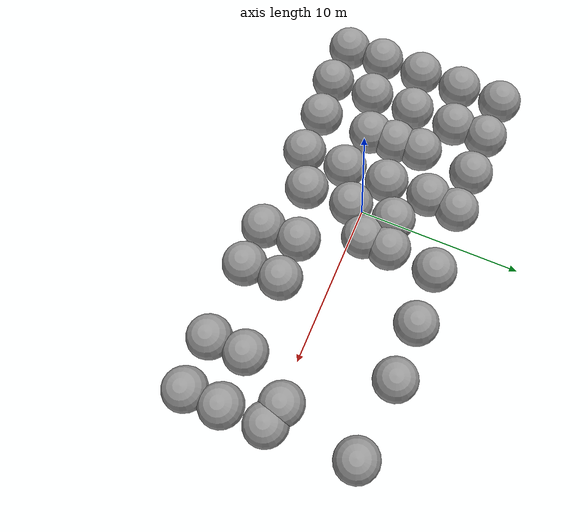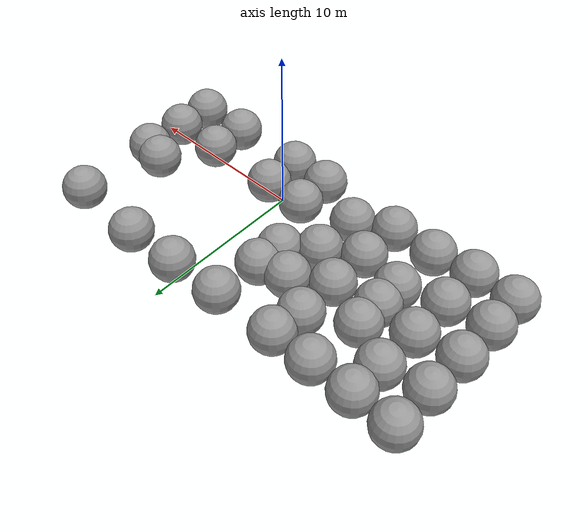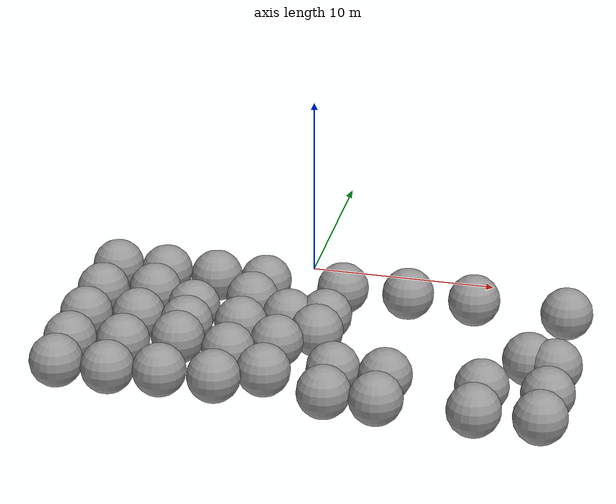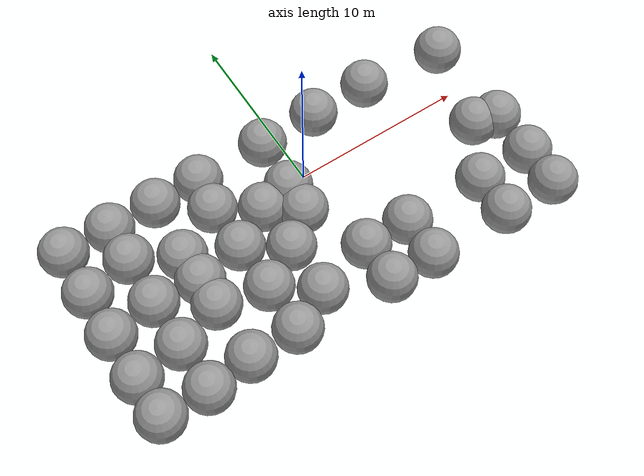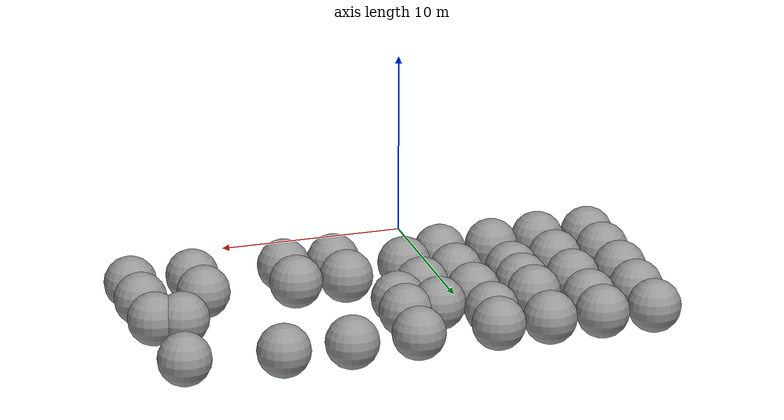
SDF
<sdf version="1.7">
 <world name="default">
  <light name="sun" type="directional">
   <pose>0 0 10 0 -0 0</pose>
   <diffuse>0.8 0.8 0.8 1</diffuse>
   <specular>0.2 0.2 0.2 1</specular>
   <attenuation>
    <range>1000</range>
    <constant>0.9</constant>
    <linear>0.01</linear>
    <quadratic>0.001</quadratic>
   </attenuation>
   <direction>-0.5 0.1 -0.9</direction>
   <spot><inner_angle>0</inner_angle><outer_angle>0</outer_angle><falloff>0</falloff></spot>
  </light>
  <gravity>0 0 -9.8</gravity>
  <magnetic_field>6e-06 2.3e-05 -4.2e-05</magnetic_field>
  <atmosphere type="adiabatic"/>
  <physics type="ode">
   <max_step_size>0.001</max_step_size>
   <real_time_factor>1</real_time_factor>
   <real_time_update_rate>1000</real_time_update_rate>
  </physics>
  <scene><ambient>0.4 0.4 0.4 1</ambient><background>0.7 0.7 0.7 1</background><shadows>1</shadows></scene>
  <spherical_coordinates>
   <surface_model>EARTH_WGS84</surface_model>
   <latitude_deg>0</latitude_deg>
   <longitude_deg>0</longitude_deg>
   <elevation>0</elevation>
   <heading_deg>0</heading_deg>
  </spherical_coordinates>
  <model name="fly_spawn_38">
   <link name="link_0">
    <inertial>
     <mass>1</mass>
     <inertia><ixx>0.1</ixx><ixy>0</ixy><ixz>0</ixz><iyy>0.1</iyy><iyz>0</iyz><izz>0.1</izz></inertia>
     <pose>0 0 -2.0 0 -0 0</pose>
    </inertial>
    <visual name="visual">
     <pose>0 0 -2.0 0 -0 0</pose>
     <geometry><sphere><radius>1.5</radius></sphere></geometry>
     <material>
      <lighting>1</lighting>
      <script><uri>file://media/materials/scripts/gazebo.material</uri><name>Gazebo/Grey</name></script>
      <shader type="pixel"><normal_map>__default__</normal_map></shader>
      <ambient>0.3 0.3 0.3 1</ambient>
      <diffuse>0.7 0.7 0.7 1</diffuse>
      <specular>0.01 0.01 0.01 1</specular>
      <emissive>0 0 0 1</emissive>
     </material>
    </visual>
    <collision name="collision">
     <pose>0 0 -2.0 0 -0 0</pose>
     <geometry><sphere><radius>1.5</radius></sphere></geometry>
     <surface>
      <friction>
       <ode><mu>1</mu><mu2>1</mu2><fdir1>0 0 0</fdir1><slip1>0</slip1><slip2>0</slip2></ode>
       <torsional>
        <coefficient>1</coefficient>
        <patch_radius>0</patch_radius>
        <surface_radius>0</surface_radius>
        <use_patch_radius>1</use_patch_radius>
        <ode><slip>0</slip></ode>
       </torsional>
      </friction>
      <bounce><restitution_coefficient>0</restitution_coefficient><threshold>1e+06</threshold></bounce>
      <contact>
       <collide_without_contact>0</collide_without_contact>
       <collide_without_contact_bitmask>1</collide_without_contact_bitmask>
       <collide_bitmask>1</collide_bitmask>
       <ode>
        <soft_cfm>0</soft_cfm>
        <soft_erp>0.2</soft_erp>
        <kp>1e+13</kp>
        <kd>1</kd>
        <max_vel>0.01</max_vel>
        <min_depth>0</min_depth>
       </ode>
       <bullet>
        <split_impulse>1</split_impulse>
        <split_impulse_penetration_threshold>-0.01</split_impulse_penetration_threshold>
        <soft_cfm>0</soft_cfm>
        <soft_erp>0.2</soft_erp>
        <kp>1e+13</kp>
        <kd>1</kd>
       </bullet>
      </contact>
     </surface>
    </collision>
   </link>
   <static>1</static>
   <pose>-13.0749 5.32969 -2.0 0 -0 0</pose>
  </model>
  <model name="fly_spawn_0">
   <link name="link_0">
    <inertial>
     <mass>1</mass>
     <inertia><ixx>0.1</ixx><ixy>0</ixy><ixz>0</ixz><iyy>0.1</iyy><iyz>0</iyz><izz>0.1</izz></inertia>
     <pose>0 0 -2.0 0 -0 0</pose>
    </inertial>
    <visual name="visual">
     <pose>0 0 -2.0 0 -0 0</pose>
     <geometry><sphere><radius>1.5</radius></sphere></geometry>
     <material>
      <lighting>1</lighting>
      <script><uri>file://media/materials/scripts/gazebo.material</uri><name>Gazebo/Grey</name></script>
      <shader type="pixel"><normal_map>__default__</normal_map></shader>
      <ambient>0.3 0.3 0.3 1</ambient>
      <diffuse>0.7 0.7 0.7 1</diffuse>
      <specular>0.01 0.01 0.01 1</specular>
      <emissive>0 0 0 1</emissive>
     </material>
    </visual>
    <collision name="collision">
     <pose>0 0 -2.0 0 -0 0</pose>
     <geometry><sphere><radius>1.5</radius></sphere></geometry>
     <surface>
      <friction>
       <ode><mu>1</mu><mu2>1</mu2><fdir1>0 0 0</fdir1><slip1>0</slip1><slip2>0</slip2></ode>
       <torsional>
        <coefficient>1</coefficient>
        <patch_radius>0</patch_radius>
        <surface_radius>0</surface_radius>
        <use_patch_radius>1</use_patch_radius>
        <ode><slip>0</slip></ode>
       </torsional>
      </friction>
      <bounce><restitution_coefficient>0</restitution_coefficient><threshold>1e+06</threshold></bounce>
      <contact>
       <collide_without_contact>0</collide_without_contact>
       <collide_without_contact_bitmask>1</collide_without_contact_bitmask>
       <collide_bitmask>1</collide_bitmask>
       <ode>
        <soft_cfm>0</soft_cfm>
        <soft_erp>0.2</soft_erp>
        <kp>1e+13</kp>
        <kd>1</kd>
        <max_vel>0.01</max_vel>
        <min_depth>0</min_depth>
       </ode>
       <bullet>
        <split_impulse>1</split_impulse>
        <split_impulse_penetration_threshold>-0.01</split_impulse_penetration_threshold>
        <soft_cfm>0</soft_cfm>
        <soft_erp>0.2</soft_erp>
        <kp>1e+13</kp>
        <kd>1</kd>
       </bullet>
      </contact>
     </surface>
    </collision>
   </link>
   <static>1</static>
   <pose>-13.0897 2.29971 -2.0 0 -0 0</pose>
  </model>
  <model name="fly_spawn_1">
   <link name="link_0">
    <inertial>
     <mass>1</mass>
     <inertia><ixx>0.1</ixx><ixy>0</ixy><ixz>0</ixz><iyy>0.1</iyy><iyz>0</iyz><izz>0.1</izz></inertia>
     <pose>0 0 -2.0 0 -0 0</pose>
    </inertial>
    <visual name="visual">
     <pose>0 0 -2.0 0 -0 0</pose>
     <geometry><sphere><radius>1.5</radius></sphere></geometry>
     <material>
      <lighting>1</lighting>
      <script><uri>file://media/materials/scripts/gazebo.material</uri><name>Gazebo/Grey</name></script>
      <shader type="pixel"><normal_map>__default__</normal_map></shader>
      <ambient>0.3 0.3 0.3 1</ambient>
      <diffuse>0.7 0.7 0.7 1</diffuse>
      <specular>0.01 0.01 0.01 1</specular>
      <emissive>0 0 0 1</emissive>
     </material>
    </visual>
    <collision name="collision">
     <pose>0 0 -2.0 0 -0 0</pose>
     <geometry><sphere><radius>1.5</radius></sphere></geometry>
     <surface>
      <friction>
       <ode><mu>1</mu><mu2>1</mu2><fdir1>0 0 0</fdir1><slip1>0</slip1><slip2>0</slip2></ode>
       <torsional>
        <coefficient>1</coefficient>
        <patch_radius>0</patch_radius>
        <surface_radius>0</surface_radius>
        <use_patch_radius>1</use_patch_radius>
        <ode><slip>0</slip></ode>
       </torsional>
      </friction>
      <bounce><restitution_coefficient>0</restitution_coefficient><threshold>1e+06</threshold></bounce>
      <contact>
       <collide_without_contact>0</collide_without_contact>
       <collide_without_contact_bitmask>1</collide_without_contact_bitmask>
       <collide_bitmask>1</collide_bitmask>
       <ode>
        <soft_cfm>0</soft_cfm>
        <soft_erp>0.2</soft_erp>
        <kp>1e+13</kp>
        <kd>1</kd>
        <max_vel>0.01</max_vel>
        <min_depth>0</min_depth>
       </ode>
       <bullet>
        <split_impulse>1</split_impulse>
        <split_impulse_penetration_threshold>-0.01</split_impulse_penetration_threshold>
        <soft_cfm>0</soft_cfm>
        <soft_erp>0.2</soft_erp>
        <kp>1e+13</kp>
        <kd>1</kd>
       </bullet>
      </contact>
     </surface>
    </collision>
   </link>
   <static>1</static>
   <pose>-13.174 -0.669702 -2.0 0 -0 0</pose>
  </model>
  <model name="fly_spawn_2">
   <link name="link_0">
    <inertial>
     <mass>1</mass>
     <inertia><ixx>0.1</ixx><ixy>0</ixy><ixz>0</ixz><iyy>0.1</iyy><iyz>0</iyz><izz>0.1</izz></inertia>
     <pose>0 0 -2.0 0 -0 0</pose>
    </inertial>
    <visual name="visual">
     <pose>0 0 -2.0 0 -0 0</pose>
     <geometry><sphere><radius>1.5</radius></sphere></geometry>
     <material>
      <lighting>1</lighting>
      <script><uri>file://media/materials/scripts/gazebo.material</uri><name>Gazebo/Grey</name></script>
      <shader type="pixel"><normal_map>__default__</normal_map></shader>
      <ambient>0.3 0.3 0.3 1</ambient>
      <diffuse>0.7 0.7 0.7 1</diffuse>
      <specular>0.01 0.01 0.01 1</specular>
      <emissive>0 0 0 1</emissive>
     </material>
    </visual>
    <collision name="collision">
     <pose>0 0 -2.0 0 -0 0</pose>
     <geometry><sphere><radius>1.5</radius></sphere></geometry>
     <surface>
      <friction>
       <ode><mu>1</mu><mu2>1</mu2><fdir1>0 0 0</fdir1><slip1>0</slip1><slip2>0</slip2></ode>
       <torsional>
        <coefficient>1</coefficient>
        <patch_radius>0</patch_radius>
        <surface_radius>0</surface_radius>
        <use_patch_radius>1</use_patch_radius>
        <ode><slip>0</slip></ode>
       </torsional>
      </friction>
      <bounce><restitution_coefficient>0</restitution_coefficient><threshold>1e+06</threshold></bounce>
      <contact>
       <collide_without_contact>0</collide_without_contact>
       <collide_without_contact_bitmask>1</collide_without_contact_bitmask>
       <collide_bitmask>1</collide_bitmask>
       <ode>
        <soft_cfm>0</soft_cfm>
        <soft_erp>0.2</soft_erp>
        <kp>1e+13</kp>
        <kd>1</kd>
        <max_vel>0.01</max_vel>
        <min_depth>0</min_depth>
       </ode>
       <bullet>
        <split_impulse>1</split_impulse>
        <split_impulse_penetration_threshold>-0.01</split_impulse_penetration_threshold>
        <soft_cfm>0</soft_cfm>
        <soft_erp>0.2</soft_erp>
        <kp>1e+13</kp>
        <kd>1</kd>
       </bullet>
      </contact>
     </surface>
    </collision>
   </link>
   <static>1</static>
   <pose>-13.1784 -3.65977 -2.0 0 -0 0</pose>
  </model>
  <model name="fly_spawn_3">
   <link name="link_0">
    <inertial>
     <mass>1</mass>
     <inertia><ixx>0.1</ixx><ixy>0</ixy><ixz>0</ixz><iyy>0.1</iyy><iyz>0</iyz><izz>0.1</izz></inertia>
     <pose>0 0 -2.0 0 -0 0</pose>
    </inertial>
    <visual name="visual">
     <pose>0 0 -2.0 0 -0 0</pose>
     <geometry><sphere><radius>1.5</radius></sphere></geometry>
     <material>
      <lighting>1</lighting>
      <script><uri>file://media/materials/scripts/gazebo.material</uri><name>Gazebo/Grey</name></script>
      <shader type="pixel"><normal_map>__default__</normal_map></shader>
      <ambient>0.3 0.3 0.3 1</ambient>
      <diffuse>0.7 0.7 0.7 1</diffuse>
      <specular>0.01 0.01 0.01 1</specular>
      <emissive>0 0 0 1</emissive>
     </material>
    </visual>
    <collision name="collision">
     <pose>0 0 -2.0 0 -0 0</pose>
     <geometry><sphere><radius>1.5</radius></sphere></geometry>
     <surface>
      <friction>
       <ode><mu>1</mu><mu2>1</mu2><fdir1>0 0 0</fdir1><slip1>0</slip1><slip2>0</slip2></ode>
       <torsional>
        <coefficient>1</coefficient>
        <patch_radius>0</patch_radius>
        <surface_radius>0</surface_radius>
        <use_patch_radius>1</use_patch_radius>
        <ode><slip>0</slip></ode>
       </torsional>
      </friction>
      <bounce><restitution_coefficient>0</restitution_coefficient><threshold>1e+06</threshold></bounce>
      <contact>
       <collide_without_contact>0</collide_without_contact>
       <collide_without_contact_bitmask>1</collide_without_contact_bitmask>
       <collide_bitmask>1</collide_bitmask>
       <ode>
        <soft_cfm>0</soft_cfm>
        <soft_erp>0.2</soft_erp>
        <kp>1e+13</kp>
        <kd>1</kd>
        <max_vel>0.01</max_vel>
        <min_depth>0</min_depth>
       </ode>
       <bullet>
        <split_impulse>1</split_impulse>
        <split_impulse_penetration_threshold>-0.01</split_impulse_penetration_threshold>
        <soft_cfm>0</soft_cfm>
        <soft_erp>0.2</soft_erp>
        <kp>1e+13</kp>
        <kd>1</kd>
       </bullet>
      </contact>
     </surface>
    </collision>
   </link>
   <static>1</static>
   <pose>-13.1495 -6.24009 -2.0 0 -0 0</pose>
  </model>
  <model name="fly_spawn_4">
   <link name="link_0">
    <inertial>
     <mass>1</mass>
     <inertia><ixx>0.1</ixx><ixy>0</ixy><ixz>0</ixz><iyy>0.1</iyy><iyz>0</iyz><izz>0.1</izz></inertia>
     <pose>0 0 -2.0 0 -0 0</pose>
    </inertial>
    <visual name="visual">
     <pose>0 0 -2.0 0 -0 0</pose>
     <geometry><sphere><radius>1.5</radius></sphere></geometry>
     <material>
      <lighting>1</lighting>
      <script><uri>file://media/materials/scripts/gazebo.material</uri><name>Gazebo/Grey</name></script>
      <shader type="pixel"><normal_map>__default__</normal_map></shader>
      <ambient>0.3 0.3 0.3 1</ambient>
      <diffuse>0.7 0.7 0.7 1</diffuse>
      <specular>0.01 0.01 0.01 1</specular>
      <emissive>0 0 0 1</emissive>
     </material>
    </visual>
    <collision name="collision">
     <pose>0 0 -2.0 0 -0 0</pose>
     <geometry><sphere><radius>1.5</radius></sphere></geometry>
     <surface>
      <friction>
       <ode><mu>1</mu><mu2>1</mu2><fdir1>0 0 0</fdir1><slip1>0</slip1><slip2>0</slip2></ode>
       <torsional>
        <coefficient>1</coefficient>
        <patch_radius>0</patch_radius>
        <surface_radius>0</surface_radius>
        <use_patch_radius>1</use_patch_radius>
        <ode><slip>0</slip></ode>
       </torsional>
      </friction>
      <bounce><restitution_coefficient>0</restitution_coefficient><threshold>1e+06</threshold></bounce>
      <contact>
       <collide_without_contact>0</collide_without_contact>
       <collide_without_contact_bitmask>1</collide_without_contact_bitmask>
       <collide_bitmask>1</collide_bitmask>
       <ode>
        <soft_cfm>0</soft_cfm>
        <soft_erp>0.2</soft_erp>
        <kp>1e+13</kp>
        <kd>1</kd>
        <max_vel>0.01</max_vel>
        <min_depth>0</min_depth>
       </ode>
       <bullet>
        <split_impulse>1</split_impulse>
        <split_impulse_penetration_threshold>-0.01</split_impulse_penetration_threshold>
        <soft_cfm>0</soft_cfm>
        <soft_erp>0.2</soft_erp>
        <kp>1e+13</kp>
        <kd>1</kd>
       </bullet>
      </contact>
     </surface>
    </collision>
   </link>
   <static>1</static>
   <pose>-10.1867 -6.30589 -2.0 0 -0 0</pose>
  </model>
  <model name="fly_spawn_5">
   <link name="link_0">
    <inertial>
     <mass>1</mass>
     <inertia><ixx>0.1</ixx><ixy>0</ixy><ixz>0</ixz><iyy>0.1</iyy><iyz>0</iyz><izz>0.1</izz></inertia>
     <pose>0 0 -2.0 0 -0 0</pose>
    </inertial>
    <visual name="visual">
     <pose>0 0 -2.0 0 -0 0</pose>
     <geometry><sphere><radius>1.5</radius></sphere></geometry>
     <material>
      <lighting>1</lighting>
      <script><uri>file://media/materials/scripts/gazebo.material</uri><name>Gazebo/Grey</name></script>
      <shader type="pixel"><normal_map>__default__</normal_map></shader>
      <ambient>0.3 0.3 0.3 1</ambient>
      <diffuse>0.7 0.7 0.7 1</diffuse>
      <specular>0.01 0.01 0.01 1</specular>
      <emissive>0 0 0 1</emissive>
     </material>
    </visual>
    <collision name="collision">
     <pose>0 0 -2.0 0 -0 0</pose>
     <geometry><sphere><radius>1.5</radius></sphere></geometry>
     <surface>
      <friction>
       <ode><mu>1</mu><mu2>1</mu2><fdir1>0 0 0</fdir1><slip1>0</slip1><slip2>0</slip2></ode>
       <torsional>
        <coefficient>1</coefficient>
        <patch_radius>0</patch_radius>
        <surface_radius>0</surface_radius>
        <use_patch_radius>1</use_patch_radius>
        <ode><slip>0</slip></ode>
       </torsional>
      </friction>
      <bounce><restitution_coefficient>0</restitution_coefficient><threshold>1e+06</threshold></bounce>
      <contact>
       <collide_without_contact>0</collide_without_contact>
       <collide_without_contact_bitmask>1</collide_without_contact_bitmask>
       <collide_bitmask>1</collide_bitmask>
       <ode>
        <soft_cfm>0</soft_cfm>
        <soft_erp>0.2</soft_erp>
        <kp>1e+13</kp>
        <kd>1</kd>
        <max_vel>0.01</max_vel>
        <min_depth>0</min_depth>
       </ode>
       <bullet>
        <split_impulse>1</split_impulse>
        <split_impulse_penetration_threshold>-0.01</split_impulse_penetration_threshold>
        <soft_cfm>0</soft_cfm>
        <soft_erp>0.2</soft_erp>
        <kp>1e+13</kp>
        <kd>1</kd>
       </bullet>
      </contact>
     </surface>
    </collision>
   </link>
   <static>1</static>
   <pose>-10.206 -3.27536 -2.0 0 -0 0</pose>
  </model>
  <model name="fly_spawn_6">
   <link name="link_0">
    <inertial>
     <mass>1</mass>
     <inertia><ixx>0.1</ixx><ixy>0</ixy><ixz>0</ixz><iyy>0.1</iyy><iyz>0</iyz><izz>0.1</izz></inertia>
     <pose>0 0 -2.0 0 -0 0</pose>
    </inertial>
    <visual name="visual">
     <pose>0 0 -2.0 0 -0 0</pose>
     <geometry><sphere><radius>1.5</radius></sphere></geometry>
     <material>
      <lighting>1</lighting>
      <script><uri>file://media/materials/scripts/gazebo.material</uri><name>Gazebo/Grey</name></script>
      <shader type="pixel"><normal_map>__default__</normal_map></shader>
      <ambient>0.3 0.3 0.3 1</ambient>
      <diffuse>0.7 0.7 0.7 1</diffuse>
      <specular>0.01 0.01 0.01 1</specular>
      <emissive>0 0 0 1</emissive>
     </material>
    </visual>
    <collision name="collision">
     <pose>0 0 -2.0 0 -0 0</pose>
     <geometry><sphere><radius>1.5</radius></sphere></geometry>
     <surface>
      <friction>
       <ode><mu>1</mu><mu2>1</mu2><fdir1>0 0 0</fdir1><slip1>0</slip1><slip2>0</slip2></ode>
       <torsional>
        <coefficient>1</coefficient>
        <patch_radius>0</patch_radius>
        <surface_radius>0</surface_radius>
        <use_patch_radius>1</use_patch_radius>
        <ode><slip>0</slip></ode>
       </torsional>
      </friction>
      <bounce><restitution_coefficient>0</restitution_coefficient><threshold>1e+06</threshold></bounce>
      <contact>
       <collide_without_contact>0</collide_without_contact>
       <collide_without_contact_bitmask>1</collide_without_contact_bitmask>
       <collide_bitmask>1</collide_bitmask>
       <ode>
        <soft_cfm>0</soft_cfm>
        <soft_erp>0.2</soft_erp>
        <kp>1e+13</kp>
        <kd>1</kd>
        <max_vel>0.01</max_vel>
        <min_depth>0</min_depth>
       </ode>
       <bullet>
        <split_impulse>1</split_impulse>
        <split_impulse_penetration_threshold>-0.01</split_impulse_penetration_threshold>
        <soft_cfm>0</soft_cfm>
        <soft_erp>0.2</soft_erp>
        <kp>1e+13</kp>
        <kd>1</kd>
       </bullet>
      </contact>
     </surface>
    </collision>
   </link>
   <static>1</static>
   <pose>-10.2147 -0.204964 -2.0 0 -0 0</pose>
  </model>
  <model name="fly_spawn_7">
   <link name="link_0">
    <inertial>
     <mass>1</mass>
     <inertia><ixx>0.1</ixx><ixy>0</ixy><ixz>0</ixz><iyy>0.1</iyy><iyz>0</iyz><izz>0.1</izz></inertia>
     <pose>0 0 -2.0 0 -0 0</pose>
    </inertial>
    <visual name="visual">
     <pose>0 0 -2.0 0 -0 0</pose>
     <geometry><sphere><radius>1.5</radius></sphere></geometry>
     <material>
      <lighting>1</lighting>
      <script><uri>file://media/materials/scripts/gazebo.material</uri><name>Gazebo/Grey</name></script>
      <shader type="pixel"><normal_map>__default__</normal_map></shader>
      <ambient>0.3 0.3 0.3 1</ambient>
      <diffuse>0.7 0.7 0.7 1</diffuse>
      <specular>0.01 0.01 0.01 1</specular>
      <emissive>0 0 0 1</emissive>
     </material>
    </visual>
    <collision name="collision">
     <pose>0 0 -2.0 0 -0 0</pose>
     <geometry><sphere><radius>1.5</radius></sphere></geometry>
     <surface>
      <friction>
       <ode><mu>1</mu><mu2>1</mu2><fdir1>0 0 0</fdir1><slip1>0</slip1><slip2>0</slip2></ode>
       <torsional>
        <coefficient>1</coefficient>
        <patch_radius>0</patch_radius>
        <surface_radius>0</surface_radius>
        <use_patch_radius>1</use_patch_radius>
        <ode><slip>0</slip></ode>
       </torsional>
      </friction>
      <bounce><restitution_coefficient>0</restitution_coefficient><threshold>1e+06</threshold></bounce>
      <contact>
       <collide_without_contact>0</collide_without_contact>
       <collide_without_contact_bitmask>1</collide_without_contact_bitmask>
       <collide_bitmask>1</collide_bitmask>
       <ode>
        <soft_cfm>0</soft_cfm>
        <soft_erp>0.2</soft_erp>
        <kp>1e+13</kp>
        <kd>1</kd>
        <max_vel>0.01</max_vel>
        <min_depth>0</min_depth>
       </ode>
       <bullet>
        <split_impulse>1</split_impulse>
        <split_impulse_penetration_threshold>-0.01</split_impulse_penetration_threshold>
        <soft_cfm>0</soft_cfm>
        <soft_erp>0.2</soft_erp>
        <kp>1e+13</kp>
        <kd>1</kd>
       </bullet>
      </contact>
     </surface>
    </collision>
   </link>
   <static>1</static>
   <pose>-10.1328 2.91422 -2.0 0 -0 0</pose>
  </model>
  <model name="fly_spawn_8">
   <link name="link_0">
    <inertial>
     <mass>1</mass>
     <inertia><ixx>0.1</ixx><ixy>0</ixy><ixz>0</ixz><iyy>0.1</iyy><iyz>0</iyz><izz>0.1</izz></inertia>
     <pose>0 0 -2.0 0 -0 0</pose>
    </inertial>
    <visual name="visual">
     <pose>0 0 -2.0 0 -0 0</pose>
     <geometry><sphere><radius>1.5</radius></sphere></geometry>
     <material>
      <lighting>1</lighting>
      <script><uri>file://media/materials/scripts/gazebo.material</uri><name>Gazebo/Grey</name></script>
      <shader type="pixel"><normal_map>__default__</normal_map></shader>
      <ambient>0.3 0.3 0.3 1</ambient>
      <diffuse>0.7 0.7 0.7 1</diffuse>
      <specular>0.01 0.01 0.01 1</specular>
      <emissive>0 0 0 1</emissive>
     </material>
    </visual>
    <collision name="collision">
     <pose>0 0 -2.0 0 -0 0</pose>
     <geometry><sphere><radius>1.5</radius></sphere></geometry>
     <surface>
      <friction>
       <ode><mu>1</mu><mu2>1</mu2><fdir1>0 0 0</fdir1><slip1>0</slip1><slip2>0</slip2></ode>
       <torsional>
        <coefficient>1</coefficient>
        <patch_radius>0</patch_radius>
        <surface_radius>0</surface_radius>
        <use_patch_radius>1</use_patch_radius>
        <ode><slip>0</slip></ode>
       </torsional>
      </friction>
      <bounce><restitution_coefficient>0</restitution_coefficient><threshold>1e+06</threshold></bounce>
      <contact>
       <collide_without_contact>0</collide_without_contact>
       <collide_without_contact_bitmask>1</collide_without_contact_bitmask>
       <collide_bitmask>1</collide_bitmask>
       <ode>
        <soft_cfm>0</soft_cfm>
        <soft_erp>0.2</soft_erp>
        <kp>1e+13</kp>
        <kd>1</kd>
        <max_vel>0.01</max_vel>
        <min_depth>0</min_depth>
       </ode>
       <bullet>
        <split_impulse>1</split_impulse>
        <split_impulse_penetration_threshold>-0.01</split_impulse_penetration_threshold>
        <soft_cfm>0</soft_cfm>
        <soft_erp>0.2</soft_erp>
        <kp>1e+13</kp>
        <kd>1</kd>
       </bullet>
      </contact>
     </surface>
    </collision>
   </link>
   <static>1</static>
   <pose>-10.091 5.28387 -2.0 0 -0 0</pose>
  </model>
  <model name="fly_spawn_9">
   <link name="link_0">
    <inertial>
     <mass>1</mass>
     <inertia><ixx>0.1</ixx><ixy>0</ixy><ixz>0</ixz><iyy>0.1</iyy><iyz>0</iyz><izz>0.1</izz></inertia>
     <pose>0 0 -2.0 0 -0 0</pose>
    </inertial>
    <visual name="visual">
     <pose>0 0 -2.0 0 -0 0</pose>
     <geometry><sphere><radius>1.5</radius></sphere></geometry>
     <material>
      <lighting>1</lighting>
      <script><uri>file://media/materials/scripts/gazebo.material</uri><name>Gazebo/Grey</name></script>
      <shader type="pixel"><normal_map>__default__</normal_map></shader>
      <ambient>0.3 0.3 0.3 1</ambient>
      <diffuse>0.7 0.7 0.7 1</diffuse>
      <specular>0.01 0.01 0.01 1</specular>
      <emissive>0 0 0 1</emissive>
     </material>
    </visual>
    <collision name="collision">
     <pose>0 0 -2.0 0 -0 0</pose>
     <geometry><sphere><radius>1.5</radius></sphere></geometry>
     <surface>
      <friction>
       <ode><mu>1</mu><mu2>1</mu2><fdir1>0 0 0</fdir1><slip1>0</slip1><slip2>0</slip2></ode>
       <torsional>
        <coefficient>1</coefficient>
        <patch_radius>0</patch_radius>
        <surface_radius>0</surface_radius>
        <use_patch_radius>1</use_patch_radius>
        <ode><slip>0</slip></ode>
       </torsional>
      </friction>
      <bounce><restitution_coefficient>0</restitution_coefficient><threshold>1e+06</threshold></bounce>
      <contact>
       <collide_without_contact>0</collide_without_contact>
       <collide_without_contact_bitmask>1</collide_without_contact_bitmask>
       <collide_bitmask>1</collide_bitmask>
       <ode>
        <soft_cfm>0</soft_cfm>
        <soft_erp>0.2</soft_erp>
        <kp>1e+13</kp>
        <kd>1</kd>
        <max_vel>0.01</max_vel>
        <min_depth>0</min_depth>
       </ode>
       <bullet>
        <split_impulse>1</split_impulse>
        <split_impulse_penetration_threshold>-0.01</split_impulse_penetration_threshold>
        <soft_cfm>0</soft_cfm>
        <soft_erp>0.2</soft_erp>
        <kp>1e+13</kp>
        <kd>1</kd>
       </bullet>
      </contact>
     </surface>
    </collision>
   </link>
   <static>1</static>
   <pose>-7.06072 5.28317 -2.0 0 -0 0</pose>
  </model>
  <model name="fly_spawn_10">
   <link name="link_0">
    <inertial>
     <mass>1</mass>
     <inertia><ixx>0.1</ixx><ixy>0</ixy><ixz>0</ixz><iyy>0.1</iyy><iyz>0</iyz><izz>0.1</izz></inertia>
     <pose>0 0 -2.0 0 -0 0</pose>
    </inertial>
    <visual name="visual">
     <pose>0 0 -2.0 0 -0 0</pose>
     <geometry><sphere><radius>1.5</radius></sphere></geometry>
     <material>
      <lighting>1</lighting>
      <script><uri>file://media/materials/scripts/gazebo.material</uri><name>Gazebo/Grey</name></script>
      <shader type="pixel"><normal_map>__default__</normal_map></shader>
      <ambient>0.3 0.3 0.3 1</ambient>
      <diffuse>0.7 0.7 0.7 1</diffuse>
      <specular>0.01 0.01 0.01 1</specular>
      <emissive>0 0 0 1</emissive>
     </material>
    </visual>
    <collision name="collision">
     <pose>0 0 -2.0 0 -0 0</pose>
     <geometry><sphere><radius>1.5</radius></sphere></geometry>
     <surface>
      <friction>
       <ode><mu>1</mu><mu2>1</mu2><fdir1>0 0 0</fdir1><slip1>0</slip1><slip2>0</slip2></ode>
       <torsional>
        <coefficient>1</coefficient>
        <patch_radius>0</patch_radius>
        <surface_radius>0</surface_radius>
        <use_patch_radius>1</use_patch_radius>
        <ode><slip>0</slip></ode>
       </torsional>
      </friction>
      <bounce><restitution_coefficient>0</restitution_coefficient><threshold>1e+06</threshold></bounce>
      <contact>
       <collide_without_contact>0</collide_without_contact>
       <collide_without_contact_bitmask>1</collide_without_contact_bitmask>
       <collide_bitmask>1</collide_bitmask>
       <ode>
        <soft_cfm>0</soft_cfm>
        <soft_erp>0.2</soft_erp>
        <kp>1e+13</kp>
        <kd>1</kd>
        <max_vel>0.01</max_vel>
        <min_depth>0</min_depth>
       </ode>
       <bullet>
        <split_impulse>1</split_impulse>
        <split_impulse_penetration_threshold>-0.01</split_impulse_penetration_threshold>
        <soft_cfm>0</soft_cfm>
        <soft_erp>0.2</soft_erp>
        <kp>1e+13</kp>
        <kd>1</kd>
       </bullet>
      </contact>
     </surface>
    </collision>
   </link>
   <static>1</static>
   <pose>-7.40093 1.43907 -2.0 0 -0 0</pose>
  </model>
  <model name="fly_spawn_11">
   <link name="link_0">
    <inertial>
     <mass>1</mass>
     <inertia><ixx>0.1</ixx><ixy>0</ixy><ixz>0</ixz><iyy>0.1</iyy><iyz>0</iyz><izz>0.1</izz></inertia>
     <pose>0 0 -2.0 0 -0 0</pose>
    </inertial>
    <visual name="visual">
     <pose>0 0 -2.0 0 -0 0</pose>
     <geometry><sphere><radius>1.5</radius></sphere></geometry>
     <material>
      <lighting>1</lighting>
      <script><uri>file://media/materials/scripts/gazebo.material</uri><name>Gazebo/Grey</name></script>
      <shader type="pixel"><normal_map>__default__</normal_map></shader>
      <ambient>0.3 0.3 0.3 1</ambient>
      <diffuse>0.7 0.7 0.7 1</diffuse>
      <specular>0.01 0.01 0.01 1</specular>
      <emissive>0 0 0 1</emissive>
     </material>
    </visual>
    <collision name="collision">
     <pose>0 0 -2.0 0 -0 0</pose>
     <geometry><sphere><radius>1.5</radius></sphere></geometry>
     <surface>
      <friction>
       <ode><mu>1</mu><mu2>1</mu2><fdir1>0 0 0</fdir1><slip1>0</slip1><slip2>0</slip2></ode>
       <torsional>
        <coefficient>1</coefficient>
        <patch_radius>0</patch_radius>
        <surface_radius>0</surface_radius>
        <use_patch_radius>1</use_patch_radius>
        <ode><slip>0</slip></ode>
       </torsional>
      </friction>
      <bounce><restitution_coefficient>0</restitution_coefficient><threshold>1e+06</threshold></bounce>
      <contact>
       <collide_without_contact>0</collide_without_contact>
       <collide_without_contact_bitmask>1</collide_without_contact_bitmask>
       <collide_bitmask>1</collide_bitmask>
       <ode>
        <soft_cfm>0</soft_cfm>
        <soft_erp>0.2</soft_erp>
        <kp>1e+13</kp>
        <kd>1</kd>
        <max_vel>0.01</max_vel>
        <min_depth>0</min_depth>
       </ode>
       <bullet>
        <split_impulse>1</split_impulse>
        <split_impulse_penetration_threshold>-0.01</split_impulse_penetration_threshold>
        <soft_cfm>0</soft_cfm>
        <soft_erp>0.2</soft_erp>
        <kp>1e+13</kp>
        <kd>1</kd>
       </bullet>
      </contact>
     </surface>
    </collision>
   </link>
   <static>1</static>
   <pose>-7.32138 -2.28074 -2.0 0 -0 0</pose>
  </model>
  <model name="fly_spawn_12">
   <link name="link_0">
    <inertial>
     <mass>1</mass>
     <inertia><ixx>0.1</ixx><ixy>0</ixy><ixz>0</ixz><iyy>0.1</iyy><iyz>0</iyz><izz>0.1</izz></inertia>
     <pose>0 0 -2.0 0 -0 0</pose>
    </inertial>
    <visual name="visual">
     <pose>0 0 -2.0 0 -0 0</pose>
     <geometry><sphere><radius>1.5</radius></sphere></geometry>
     <material>
      <lighting>1</lighting>
      <script><uri>file://media/materials/scripts/gazebo.material</uri><name>Gazebo/Grey</name></script>
      <shader type="pixel"><normal_map>__default__</normal_map></shader>
      <ambient>0.3 0.3 0.3 1</ambient>
      <diffuse>0.7 0.7 0.7 1</diffuse>
      <specular>0.01 0.01 0.01 1</specular>
      <emissive>0 0 0 1</emissive>
     </material>
    </visual>
    <collision name="collision">
     <pose>0 0 -2.0 0 -0 0</pose>
     <geometry><sphere><radius>1.5</radius></sphere></geometry>
     <surface>
      <friction>
       <ode><mu>1</mu><mu2>1</mu2><fdir1>0 0 0</fdir1><slip1>0</slip1><slip2>0</slip2></ode>
       <torsional>
        <coefficient>1</coefficient>
        <patch_radius>0</patch_radius>
        <surface_radius>0</surface_radius>
        <use_patch_radius>1</use_patch_radius>
        <ode><slip>0</slip></ode>
       </torsional>
      </friction>
      <bounce><restitution_coefficient>0</restitution_coefficient><threshold>1e+06</threshold></bounce>
      <contact>
       <collide_without_contact>0</collide_without_contact>
       <collide_without_contact_bitmask>1</collide_without_contact_bitmask>
       <collide_bitmask>1</collide_bitmask>
       <ode>
        <soft_cfm>0</soft_cfm>
        <soft_erp>0.2</soft_erp>
        <kp>1e+13</kp>
        <kd>1</kd>
        <max_vel>0.01</max_vel>
        <min_depth>0</min_depth>
       </ode>
       <bullet>
        <split_impulse>1</split_impulse>
        <split_impulse_penetration_threshold>-0.01</split_impulse_penetration_threshold>
        <soft_cfm>0</soft_cfm>
        <soft_erp>0.2</soft_erp>
        <kp>1e+13</kp>
        <kd>1</kd>
       </bullet>
      </contact>
     </surface>
    </collision>
   </link>
   <static>1</static>
   <pose>-7.32608 -0.450745 -2.0 0 -0 0</pose>
  </model>
  <model name="fly_spawn_13">
   <link name="link_0">
    <inertial>
     <mass>1</mass>
     <inertia><ixx>0.1</ixx><ixy>0</ixy><ixz>0</ixz><iyy>0.1</iyy><iyz>0</iyz><izz>0.1</izz></inertia>
     <pose>0 0 -2.0 0 -0 0</pose>
    </inertial>
    <visual name="visual">
     <pose>0 0 -2.0 0 -0 0</pose>
     <geometry><sphere><radius>1.5</radius></sphere></geometry>
     <material>
      <lighting>1</lighting>
      <script><uri>file://media/materials/scripts/gazebo.material</uri><name>Gazebo/Grey</name></script>
      <shader type="pixel"><normal_map>__default__</normal_map></shader>
      <ambient>0.3 0.3 0.3 1</ambient>
      <diffuse>0.7 0.7 0.7 1</diffuse>
      <specular>0.01 0.01 0.01 1</specular>
      <emissive>0 0 0 1</emissive>
     </material>
    </visual>
    <collision name="collision">
     <pose>0 0 -2.0 0 -0 0</pose>
     <geometry><sphere><radius>1.5</radius></sphere></geometry>
     <surface>
      <friction>
       <ode><mu>1</mu><mu2>1</mu2><fdir1>0 0 0</fdir1><slip1>0</slip1><slip2>0</slip2></ode>
       <torsional>
        <coefficient>1</coefficient>
        <patch_radius>0</patch_radius>
        <surface_radius>0</surface_radius>
        <use_patch_radius>1</use_patch_radius>
        <ode><slip>0</slip></ode>
       </torsional>
      </friction>
      <bounce><restitution_coefficient>0</restitution_coefficient><threshold>1e+06</threshold></bounce>
      <contact>
       <collide_without_contact>0</collide_without_contact>
       <collide_without_contact_bitmask>1</collide_without_contact_bitmask>
       <collide_bitmask>1</collide_bitmask>
       <ode>
        <soft_cfm>0</soft_cfm>
        <soft_erp>0.2</soft_erp>
        <kp>1e+13</kp>
        <kd>1</kd>
        <max_vel>0.01</max_vel>
        <min_depth>0</min_depth>
       </ode>
       <bullet>
        <split_impulse>1</split_impulse>
        <split_impulse_penetration_threshold>-0.01</split_impulse_penetration_threshold>
        <soft_cfm>0</soft_cfm>
        <soft_erp>0.2</soft_erp>
        <kp>1e+13</kp>
        <kd>1</kd>
       </bullet>
      </contact>
     </surface>
    </collision>
   </link>
   <static>1</static>
   <pose>-7.33183 -6.00078 -2.0 0 -0 0</pose>
  </model>
  <model name="fly_spawn_14">
   <link name="link_0">
    <inertial>
     <mass>1</mass>
     <inertia><ixx>0.1</ixx><ixy>0</ixy><ixz>0</ixz><iyy>0.1</iyy><iyz>0</iyz><izz>0.1</izz></inertia>
     <pose>0 0 -2.0 0 -0 0</pose>
    </inertial>
    <visual name="visual">
     <pose>0 0 -2.0 0 -0 0</pose>
     <geometry><sphere><radius>1.5</radius></sphere></geometry>
     <material>
      <lighting>1</lighting>
      <script><uri>file://media/materials/scripts/gazebo.material</uri><name>Gazebo/Grey</name></script>
      <shader type="pixel"><normal_map>__default__</normal_map></shader>
      <ambient>0.3 0.3 0.3 1</ambient>
      <diffuse>0.7 0.7 0.7 1</diffuse>
      <specular>0.01 0.01 0.01 1</specular>
      <emissive>0 0 0 1</emissive>
     </material>
    </visual>
    <collision name="collision">
     <pose>0 0 -2.0 0 -0 0</pose>
     <geometry><sphere><radius>1.5</radius></sphere></geometry>
     <surface>
      <friction>
       <ode><mu>1</mu><mu2>1</mu2><fdir1>0 0 0</fdir1><slip1>0</slip1><slip2>0</slip2></ode>
       <torsional>
        <coefficient>1</coefficient>
        <patch_radius>0</patch_radius>
        <surface_radius>0</surface_radius>
        <use_patch_radius>1</use_patch_radius>
        <ode><slip>0</slip></ode>
       </torsional>
      </friction>
      <bounce><restitution_coefficient>0</restitution_coefficient><threshold>1e+06</threshold></bounce>
      <contact>
       <collide_without_contact>0</collide_without_contact>
       <collide_without_contact_bitmask>1</collide_without_contact_bitmask>
       <collide_bitmask>1</collide_bitmask>
       <ode>
        <soft_cfm>0</soft_cfm>
        <soft_erp>0.2</soft_erp>
        <kp>1e+13</kp>
        <kd>1</kd>
        <max_vel>0.01</max_vel>
        <min_depth>0</min_depth>
       </ode>
       <bullet>
        <split_impulse>1</split_impulse>
        <split_impulse_penetration_threshold>-0.01</split_impulse_penetration_threshold>
        <soft_cfm>0</soft_cfm>
        <soft_erp>0.2</soft_erp>
        <kp>1e+13</kp>
        <kd>1</kd>
       </bullet>
      </contact>
     </surface>
    </collision>
   </link>
   <static>1</static>
   <pose>-4.2645 -5.98653 -2.0 0 -0 0</pose>
  </model>
  <model name="fly_spawn_15">
   <link name="link_0">
    <inertial>
     <mass>1</mass>
     <inertia><ixx>0.1</ixx><ixy>0</ixy><ixz>0</ixz><iyy>0.1</iyy><iyz>0</iyz><izz>0.1</izz></inertia>
     <pose>0 0 -2.0 0 -0 0</pose>
    </inertial>
    <visual name="visual">
     <pose>0 0 -2.0 0 -0 0</pose>
     <geometry><sphere><radius>1.5</radius></sphere></geometry>
     <material>
      <lighting>1</lighting>
      <script><uri>file://media/materials/scripts/gazebo.material</uri><name>Gazebo/Grey</name></script>
      <shader type="pixel"><normal_map>__default__</normal_map></shader>
      <ambient>0.3 0.3 0.3 1</ambient>
      <diffuse>0.7 0.7 0.7 1</diffuse>
      <specular>0.01 0.01 0.01 1</specular>
      <emissive>0 0 0 1</emissive>
     </material>
    </visual>
    <collision name="collision">
     <pose>0 0 -2.0 0 -0 0</pose>
     <geometry><sphere><radius>1.5</radius></sphere></geometry>
     <surface>
      <friction>
       <ode><mu>1</mu><mu2>1</mu2><fdir1>0 0 0</fdir1><slip1>0</slip1><slip2>0</slip2></ode>
       <torsional>
        <coefficient>1</coefficient>
        <patch_radius>0</patch_radius>
        <surface_radius>0</surface_radius>
        <use_patch_radius>1</use_patch_radius>
        <ode><slip>0</slip></ode>
       </torsional>
      </friction>
      <bounce><restitution_coefficient>0</restitution_coefficient><threshold>1e+06</threshold></bounce>
      <contact>
       <collide_without_contact>0</collide_without_contact>
       <collide_without_contact_bitmask>1</collide_without_contact_bitmask>
       <collide_bitmask>1</collide_bitmask>
       <ode>
        <soft_cfm>0</soft_cfm>
        <soft_erp>0.2</soft_erp>
        <kp>1e+13</kp>
        <kd>1</kd>
        <max_vel>0.01</max_vel>
        <min_depth>0</min_depth>
       </ode>
       <bullet>
        <split_impulse>1</split_impulse>
        <split_impulse_penetration_threshold>-0.01</split_impulse_penetration_threshold>
        <soft_cfm>0</soft_cfm>
        <soft_erp>0.2</soft_erp>
        <kp>1e+13</kp>
        <kd>1</kd>
       </bullet>
      </contact>
     </surface>
    </collision>
   </link>
   <static>1</static>
   <pose>-4.24353 -2.93654 -2.0 0 -0 0</pose>
  </model>
  <model name="fly_spawn_16">
   <link name="link_0">
    <inertial>
     <mass>1</mass>
     <inertia><ixx>0.1</ixx><ixy>0</ixy><ixz>0</ixz><iyy>0.1</iyy><iyz>0</iyz><izz>0.1</izz></inertia>
     <pose>0 0 -2.0 0 -0 0</pose>
    </inertial>
    <visual name="visual">
     <pose>0 0 -2.0 0 -0 0</pose>
     <geometry><sphere><radius>1.5</radius></sphere></geometry>
     <material>
      <lighting>1</lighting>
      <script><uri>file://media/materials/scripts/gazebo.material</uri><name>Gazebo/Grey</name></script>
      <shader type="pixel"><normal_map>__default__</normal_map></shader>
      <ambient>0.3 0.3 0.3 1</ambient>
      <diffuse>0.7 0.7 0.7 1</diffuse>
      <specular>0.01 0.01 0.01 1</specular>
      <emissive>0 0 0 1</emissive>
     </material>
    </visual>
    <collision name="collision">
     <pose>0 0 -2.0 0 -0 0</pose>
     <geometry><sphere><radius>1.5</radius></sphere></geometry>
     <surface>
      <friction>
       <ode><mu>1</mu><mu2>1</mu2><fdir1>0 0 0</fdir1><slip1>0</slip1><slip2>0</slip2></ode>
       <torsional>
        <coefficient>1</coefficient>
        <patch_radius>0</patch_radius>
        <surface_radius>0</surface_radius>
        <use_patch_radius>1</use_patch_radius>
        <ode><slip>0</slip></ode>
       </torsional>
      </friction>
      <bounce><restitution_coefficient>0</restitution_coefficient><threshold>1e+06</threshold></bounce>
      <contact>
       <collide_without_contact>0</collide_without_contact>
       <collide_without_contact_bitmask>1</collide_without_contact_bitmask>
       <collide_bitmask>1</collide_bitmask>
       <ode>
        <soft_cfm>0</soft_cfm>
        <soft_erp>0.2</soft_erp>
        <kp>1e+13</kp>
        <kd>1</kd>
        <max_vel>0.01</max_vel>
        <min_depth>0</min_depth>
       </ode>
       <bullet>
        <split_impulse>1</split_impulse>
        <split_impulse_penetration_threshold>-0.01</split_impulse_penetration_threshold>
        <soft_cfm>0</soft_cfm>
        <soft_erp>0.2</soft_erp>
        <kp>1e+13</kp>
        <kd>1</kd>
       </bullet>
      </contact>
     </surface>
    </collision>
   </link>
   <static>1</static>
   <pose>-4.30242 0.124528 -2.0 0 -0 0</pose>
  </model>
  <model name="fly_spawn_17">
   <link name="link_0">
    <inertial>
     <mass>1</mass>
     <inertia><ixx>0.1</ixx><ixy>0</ixy><ixz>0</ixz><iyy>0.1</iyy><iyz>0</iyz><izz>0.1</izz></inertia>
     <pose>0 0 -2.0 0 -0 0</pose>
    </inertial>
    <visual name="visual">
     <pose>0 0 -2.0 0 -0 0</pose>
     <geometry><sphere><radius>1.5</radius></sphere></geometry>
     <material>
      <lighting>1</lighting>
      <script><uri>file://media/materials/scripts/gazebo.material</uri><name>Gazebo/Grey</name></script>
      <shader type="pixel"><normal_map>__default__</normal_map></shader>
      <ambient>0.3 0.3 0.3 1</ambient>
      <diffuse>0.7 0.7 0.7 1</diffuse>
      <specular>0.01 0.01 0.01 1</specular>
      <emissive>0 0 0 1</emissive>
     </material>
    </visual>
    <collision name="collision">
     <pose>0 0 -2.0 0 -0 0</pose>
     <geometry><sphere><radius>1.5</radius></sphere></geometry>
     <surface>
      <friction>
       <ode><mu>1</mu><mu2>1</mu2><fdir1>0 0 0</fdir1><slip1>0</slip1><slip2>0</slip2></ode>
       <torsional>
        <coefficient>1</coefficient>
        <patch_radius>0</patch_radius>
        <surface_radius>0</surface_radius>
        <use_patch_radius>1</use_patch_radius>
        <ode><slip>0</slip></ode>
       </torsional>
      </friction>
      <bounce><restitution_coefficient>0</restitution_coefficient><threshold>1e+06</threshold></bounce>
      <contact>
       <collide_without_contact>0</collide_without_contact>
       <collide_without_contact_bitmask>1</collide_without_contact_bitmask>
       <collide_bitmask>1</collide_bitmask>
       <ode>
        <soft_cfm>0</soft_cfm>
        <soft_erp>0.2</soft_erp>
        <kp>1e+13</kp>
        <kd>1</kd>
        <max_vel>0.01</max_vel>
        <min_depth>0</min_depth>
       </ode>
       <bullet>
        <split_impulse>1</split_impulse>
        <split_impulse_penetration_threshold>-0.01</split_impulse_penetration_threshold>
        <soft_cfm>0</soft_cfm>
        <soft_erp>0.2</soft_erp>
        <kp>1e+13</kp>
        <kd>1</kd>
       </bullet>
      </contact>
     </surface>
    </collision>
   </link>
   <static>1</static>
   <pose>-4.39198 3.136 -2.0 0 -0 0</pose>
  </model>
  <model name="fly_spawn_18">
   <link name="link_0">
    <inertial>
     <mass>1</mass>
     <inertia><ixx>0.1</ixx><ixy>0</ixy><ixz>0</ixz><iyy>0.1</iyy><iyz>0</iyz><izz>0.1</izz></inertia>
     <pose>0 0 -2.0 0 -0 0</pose>
    </inertial>
    <visual name="visual">
     <pose>0 0 -2.0 0 -0 0</pose>
     <geometry><sphere><radius>1.5</radius></sphere></geometry>
     <material>
      <lighting>1</lighting>
      <script><uri>file://media/materials/scripts/gazebo.material</uri><name>Gazebo/Grey</name></script>
      <shader type="pixel"><normal_map>__default__</normal_map></shader>
      <ambient>0.3 0.3 0.3 1</ambient>
      <diffuse>0.7 0.7 0.7 1</diffuse>
      <specular>0.01 0.01 0.01 1</specular>
      <emissive>0 0 0 1</emissive>
     </material>
    </visual>
    <collision name="collision">
     <pose>0 0 -2.0 0 -0 0</pose>
     <geometry><sphere><radius>1.5</radius></sphere></geometry>
     <surface>
      <friction>
       <ode><mu>1</mu><mu2>1</mu2><fdir1>0 0 0</fdir1><slip1>0</slip1><slip2>0</slip2></ode>
       <torsional>
        <coefficient>1</coefficient>
        <patch_radius>0</patch_radius>
        <surface_radius>0</surface_radius>
        <use_patch_radius>1</use_patch_radius>
        <ode><slip>0</slip></ode>
       </torsional>
      </friction>
      <bounce><restitution_coefficient>0</restitution_coefficient><threshold>1e+06</threshold></bounce>
      <contact>
       <collide_without_contact>0</collide_without_contact>
       <collide_without_contact_bitmask>1</collide_without_contact_bitmask>
       <collide_bitmask>1</collide_bitmask>
       <ode>
        <soft_cfm>0</soft_cfm>
        <soft_erp>0.2</soft_erp>
        <kp>1e+13</kp>
        <kd>1</kd>
        <max_vel>0.01</max_vel>
        <min_depth>0</min_depth>
       </ode>
       <bullet>
        <split_impulse>1</split_impulse>
        <split_impulse_penetration_threshold>-0.01</split_impulse_penetration_threshold>
        <soft_cfm>0</soft_cfm>
        <soft_erp>0.2</soft_erp>
        <kp>1e+13</kp>
        <kd>1</kd>
       </bullet>
      </contact>
     </surface>
    </collision>
   </link>
   <static>1</static>
   <pose>-4.10298 5.29232 -2.0 0 -0 0</pose>
  </model>
  <model name="fly_spawn_19">
   <link name="link_0">
    <inertial>
     <mass>1</mass>
     <inertia><ixx>0.1</ixx><ixy>0</ixy><ixz>0</ixz><iyy>0.1</iyy><iyz>0</iyz><izz>0.1</izz></inertia>
     <pose>0 0 -2.0 0 -0 0</pose>
    </inertial>
    <visual name="visual">
     <pose>0 0 -2.0 0 -0 0</pose>
     <geometry><sphere><radius>1.5</radius></sphere></geometry>
     <material>
      <lighting>1</lighting>
      <script><uri>file://media/materials/scripts/gazebo.material</uri><name>Gazebo/Grey</name></script>
      <shader type="pixel"><normal_map>__default__</normal_map></shader>
      <ambient>0.3 0.3 0.3 1</ambient>
      <diffuse>0.7 0.7 0.7 1</diffuse>
      <specular>0.01 0.01 0.01 1</specular>
      <emissive>0 0 0 1</emissive>
     </material>
    </visual>
    <collision name="collision">
     <pose>0 0 -2.0 0 -0 0</pose>
     <geometry><sphere><radius>1.5</radius></sphere></geometry>
     <surface>
      <friction>
       <ode><mu>1</mu><mu2>1</mu2><fdir1>0 0 0</fdir1><slip1>0</slip1><slip2>0</slip2></ode>
       <torsional>
        <coefficient>1</coefficient>
        <patch_radius>0</patch_radius>
        <surface_radius>0</surface_radius>
        <use_patch_radius>1</use_patch_radius>
        <ode><slip>0</slip></ode>
       </torsional>
      </friction>
      <bounce><restitution_coefficient>0</restitution_coefficient><threshold>1e+06</threshold></bounce>
      <contact>
       <collide_without_contact>0</collide_without_contact>
       <collide_without_contact_bitmask>1</collide_without_contact_bitmask>
       <collide_bitmask>1</collide_bitmask>
       <ode>
        <soft_cfm>0</soft_cfm>
        <soft_erp>0.2</soft_erp>
        <kp>1e+13</kp>
        <kd>1</kd>
        <max_vel>0.01</max_vel>
        <min_depth>0</min_depth>
       </ode>
       <bullet>
        <split_impulse>1</split_impulse>
        <split_impulse_penetration_threshold>-0.01</split_impulse_penetration_threshold>
        <soft_cfm>0</soft_cfm>
        <soft_erp>0.2</soft_erp>
        <kp>1e+13</kp>
        <kd>1</kd>
       </bullet>
      </contact>
     </surface>
    </collision>
   </link>
   <static>1</static>
   <pose>-1.85276 1.57176 -2.0 0 -0 0</pose>
  </model>
  <model name="fly_spawn_20">
   <link name="link_0">
    <inertial>
     <mass>1</mass>
     <inertia><ixx>0.1</ixx><ixy>0</ixy><ixz>0</ixz><iyy>0.1</iyy><iyz>0</iyz><izz>0.1</izz></inertia>
     <pose>0 0 -2.0 0 -0 0</pose>
    </inertial>
    <visual name="visual">
     <pose>0 0 -2.0 0 -0 0</pose>
     <geometry><sphere><radius>1.5</radius></sphere></geometry>
     <material>
      <lighting>1</lighting>
      <script><uri>file://media/materials/scripts/gazebo.material</uri><name>Gazebo/Grey</name></script>
      <shader type="pixel"><normal_map>__default__</normal_map></shader>
      <ambient>0.3 0.3 0.3 1</ambient>
      <diffuse>0.7 0.7 0.7 1</diffuse>
      <specular>0.01 0.01 0.01 1</specular>
      <emissive>0 0 0 1</emissive>
     </material>
    </visual>
    <collision name="collision">
     <pose>0 0 -2.0 0 -0 0</pose>
     <geometry><sphere><radius>1.5</radius></sphere></geometry>
     <surface>
      <friction>
       <ode><mu>1</mu><mu2>1</mu2><fdir1>0 0 0</fdir1><slip1>0</slip1><slip2>0</slip2></ode>
       <torsional>
        <coefficient>1</coefficient>
        <patch_radius>0</patch_radius>
        <surface_radius>0</surface_radius>
        <use_patch_radius>1</use_patch_radius>
        <ode><slip>0</slip></ode>
       </torsional>
      </friction>
      <bounce><restitution_coefficient>0</restitution_coefficient><threshold>1e+06</threshold></bounce>
      <contact>
       <collide_without_contact>0</collide_without_contact>
       <collide_without_contact_bitmask>1</collide_without_contact_bitmask>
       <collide_bitmask>1</collide_bitmask>
       <ode>
        <soft_cfm>0</soft_cfm>
        <soft_erp>0.2</soft_erp>
        <kp>1e+13</kp>
        <kd>1</kd>
        <max_vel>0.01</max_vel>
        <min_depth>0</min_depth>
       </ode>
       <bullet>
        <split_impulse>1</split_impulse>
        <split_impulse_penetration_threshold>-0.01</split_impulse_penetration_threshold>
        <soft_cfm>0</soft_cfm>
        <soft_erp>0.2</soft_erp>
        <kp>1e+13</kp>
        <kd>1</kd>
       </bullet>
      </contact>
     </surface>
    </collision>
   </link>
   <static>1</static>
   <pose>-1.81387 -1.48904 -2.0 0 -0 0</pose>
  </model>
  <model name="fly_spawn_21">
   <link name="link_0">
    <inertial>
     <mass>1</mass>
     <inertia><ixx>0.1</ixx><ixy>0</ixy><ixz>0</ixz><iyy>0.1</iyy><iyz>0</iyz><izz>0.1</izz></inertia>
     <pose>0 0 -2.0 0 -0 0</pose>
    </inertial>
    <visual name="visual">
     <pose>0 0 -2.0 0 -0 0</pose>
     <geometry><sphere><radius>1.5</radius></sphere></geometry>
     <material>
      <lighting>1</lighting>
      <script><uri>file://media/materials/scripts/gazebo.material</uri><name>Gazebo/Grey</name></script>
      <shader type="pixel"><normal_map>__default__</normal_map></shader>
      <ambient>0.3 0.3 0.3 1</ambient>
      <diffuse>0.7 0.7 0.7 1</diffuse>
      <specular>0.01 0.01 0.01 1</specular>
      <emissive>0 0 0 1</emissive>
     </material>
    </visual>
    <collision name="collision">
     <pose>0 0 -2.0 0 -0 0</pose>
     <geometry><sphere><radius>1.5</radius></sphere></geometry>
     <surface>
      <friction>
       <ode><mu>1</mu><mu2>1</mu2><fdir1>0 0 0</fdir1><slip1>0</slip1><slip2>0</slip2></ode>
       <torsional>
        <coefficient>1</coefficient>
        <patch_radius>0</patch_radius>
        <surface_radius>0</surface_radius>
        <use_patch_radius>1</use_patch_radius>
        <ode><slip>0</slip></ode>
       </torsional>
      </friction>
      <bounce><restitution_coefficient>0</restitution_coefficient><threshold>1e+06</threshold></bounce>
      <contact>
       <collide_without_contact>0</collide_without_contact>
       <collide_without_contact_bitmask>1</collide_without_contact_bitmask>
       <collide_bitmask>1</collide_bitmask>
       <ode>
        <soft_cfm>0</soft_cfm>
        <soft_erp>0.2</soft_erp>
        <kp>1e+13</kp>
        <kd>1</kd>
        <max_vel>0.01</max_vel>
        <min_depth>0</min_depth>
       </ode>
       <bullet>
        <split_impulse>1</split_impulse>
        <split_impulse_penetration_threshold>-0.01</split_impulse_penetration_threshold>
        <soft_cfm>0</soft_cfm>
        <soft_erp>0.2</soft_erp>
        <kp>1e+13</kp>
        <kd>1</kd>
       </bullet>
      </contact>
     </surface>
    </collision>
   </link>
   <static>1</static>
   <pose>-1.77766 -4.74982 -2.0 0 -0 0</pose>
  </model>
  <model name="fly_spawn_22">
   <link name="link_0">
    <inertial>
     <mass>1</mass>
     <inertia><ixx>0.1</ixx><ixy>0</ixy><ixz>0</ixz><iyy>0.1</iyy><iyz>0</iyz><izz>0.1</izz></inertia>
     <pose>0 0 -2.0 0 -0 0</pose>
    </inertial>
    <visual name="visual">
     <pose>0 0 -2.0 0 -0 0</pose>
     <geometry><sphere><radius>1.5</radius></sphere></geometry>
     <material>
      <lighting>1</lighting>
      <script><uri>file://media/materials/scripts/gazebo.material</uri><name>Gazebo/Grey</name></script>
      <shader type="pixel"><normal_map>__default__</normal_map></shader>
      <ambient>0.3 0.3 0.3 1</ambient>
      <diffuse>0.7 0.7 0.7 1</diffuse>
      <specular>0.01 0.01 0.01 1</specular>
      <emissive>0 0 0 1</emissive>
     </material>
    </visual>
    <collision name="collision">
     <pose>0 0 -2.0 0 -0 0</pose>
     <geometry><sphere><radius>1.5</radius></sphere></geometry>
     <surface>
      <friction>
       <ode><mu>1</mu><mu2>1</mu2><fdir1>0 0 0</fdir1><slip1>0</slip1><slip2>0</slip2></ode>
       <torsional>
        <coefficient>1</coefficient>
        <patch_radius>0</patch_radius>
        <surface_radius>0</surface_radius>
        <use_patch_radius>1</use_patch_radius>
        <ode><slip>0</slip></ode>
       </torsional>
      </friction>
      <bounce><restitution_coefficient>0</restitution_coefficient><threshold>1e+06</threshold></bounce>
      <contact>
       <collide_without_contact>0</collide_without_contact>
       <collide_without_contact_bitmask>1</collide_without_contact_bitmask>
       <collide_bitmask>1</collide_bitmask>
       <ode>
        <soft_cfm>0</soft_cfm>
        <soft_erp>0.2</soft_erp>
        <kp>1e+13</kp>
        <kd>1</kd>
        <max_vel>0.01</max_vel>
        <min_depth>0</min_depth>
       </ode>
       <bullet>
        <split_impulse>1</split_impulse>
        <split_impulse_penetration_threshold>-0.01</split_impulse_penetration_threshold>
        <soft_cfm>0</soft_cfm>
        <soft_erp>0.2</soft_erp>
        <kp>1e+13</kp>
        <kd>1</kd>
       </bullet>
      </contact>
     </surface>
    </collision>
   </link>
   <static>1</static>
   <pose>0.088654 0.175545 -2.0 0 -0 0</pose>
  </model>
  <model name="fly_spawn_23">
   <link name="link_0">
    <inertial>
     <mass>1</mass>
     <inertia><ixx>0.1</ixx><ixy>0</ixy><ixz>0</ixz><iyy>0.1</iyy><iyz>0</iyz><izz>0.1</izz></inertia>
     <pose>0 0 -2.0 0 -0 0</pose>
    </inertial>
    <visual name="visual">
     <pose>0 0 -2.0 0 -0 0</pose>
     <geometry><sphere><radius>1.5</radius></sphere></geometry>
     <material>
      <lighting>1</lighting>
      <script><uri>file://media/materials/scripts/gazebo.material</uri><name>Gazebo/Grey</name></script>
      <shader type="pixel"><normal_map>__default__</normal_map></shader>
      <ambient>0.3 0.3 0.3 1</ambient>
      <diffuse>0.7 0.7 0.7 1</diffuse>
      <specular>0.01 0.01 0.01 1</specular>
      <emissive>0 0 0 1</emissive>
     </material>
    </visual>
    <collision name="collision">
     <pose>0 0 -2.0 0 -0 0</pose>
     <geometry><sphere><radius>1.5</radius></sphere></geometry>
     <surface>
      <friction>
       <ode><mu>1</mu><mu2>1</mu2><fdir1>0 0 0</fdir1><slip1>0</slip1><slip2>0</slip2></ode>
       <torsional>
        <coefficient>1</coefficient>
        <patch_radius>0</patch_radius>
        <surface_radius>0</surface_radius>
        <use_patch_radius>1</use_patch_radius>
        <ode><slip>0</slip></ode>
       </torsional>
      </friction>
      <bounce><restitution_coefficient>0</restitution_coefficient><threshold>1e+06</threshold></bounce>
      <contact>
       <collide_without_contact>0</collide_without_contact>
       <collide_without_contact_bitmask>1</collide_without_contact_bitmask>
       <collide_bitmask>1</collide_bitmask>
       <ode>
        <soft_cfm>0</soft_cfm>
        <soft_erp>0.2</soft_erp>
        <kp>1e+13</kp>
        <kd>1</kd>
        <max_vel>0.01</max_vel>
        <min_depth>0</min_depth>
       </ode>
       <bullet>
        <split_impulse>1</split_impulse>
        <split_impulse_penetration_threshold>-0.01</split_impulse_penetration_threshold>
        <soft_cfm>0</soft_cfm>
        <soft_erp>0.2</soft_erp>
        <kp>1e+13</kp>
        <kd>1</kd>
       </bullet>
      </contact>
     </surface>
    </collision>
   </link>
   <static>1</static>
   <pose>0.193497 2.0243 -2.0 0 -0 0</pose>
  </model>
  <model name="fly_spawn_24">
   <link name="link_0">
    <inertial>
     <mass>1</mass>
     <inertia><ixx>0.1</ixx><ixy>0</ixy><ixz>0</ixz><iyy>0.1</iyy><iyz>0</iyz><izz>0.1</izz></inertia>
     <pose>0 0 -2.0 0 -0 0</pose>
    </inertial>
    <visual name="visual">
     <pose>0 0 -2.0 0 -0 0</pose>
     <geometry><sphere><radius>1.5</radius></sphere></geometry>
     <material>
      <lighting>1</lighting>
      <script><uri>file://media/materials/scripts/gazebo.material</uri><name>Gazebo/Grey</name></script>
      <shader type="pixel"><normal_map>__default__</normal_map></shader>
      <ambient>0.3 0.3 0.3 1</ambient>
      <diffuse>0.7 0.7 0.7 1</diffuse>
      <specular>0.01 0.01 0.01 1</specular>
      <emissive>0 0 0 1</emissive>
     </material>
    </visual>
    <collision name="collision">
     <pose>0 0 -2.0 0 -0 0</pose>
     <geometry><sphere><radius>1.5</radius></sphere></geometry>
     <surface>
      <friction>
       <ode><mu>1</mu><mu2>1</mu2><fdir1>0 0 0</fdir1><slip1>0</slip1><slip2>0</slip2></ode>
       <torsional>
        <coefficient>1</coefficient>
        <patch_radius>0</patch_radius>
        <surface_radius>0</surface_radius>
        <use_patch_radius>1</use_patch_radius>
        <ode><slip>0</slip></ode>
       </torsional>
      </friction>
      <bounce><restitution_coefficient>0</restitution_coefficient><threshold>1e+06</threshold></bounce>
      <contact>
       <collide_without_contact>0</collide_without_contact>
       <collide_without_contact_bitmask>1</collide_without_contact_bitmask>
       <collide_bitmask>1</collide_bitmask>
       <ode>
        <soft_cfm>0</soft_cfm>
        <soft_erp>0.2</soft_erp>
        <kp>1e+13</kp>
        <kd>1</kd>
        <max_vel>0.01</max_vel>
        <min_depth>0</min_depth>
       </ode>
       <bullet>
        <split_impulse>1</split_impulse>
        <split_impulse_penetration_threshold>-0.01</split_impulse_penetration_threshold>
        <soft_cfm>0</soft_cfm>
        <soft_erp>0.2</soft_erp>
        <kp>1e+13</kp>
        <kd>1</kd>
       </bullet>
      </contact>
     </surface>
    </collision>
   </link>
   <static>1</static>
   <pose>0.468475 5.37091 -2.0 0 -0 0</pose>
  </model>
  <model name="fly_spawn_25">
   <link name="link_0">
    <inertial>
     <mass>1</mass>
     <inertia><ixx>0.1</ixx><ixy>0</ixy><ixz>0</ixz><iyy>0.1</iyy><iyz>0</iyz><izz>0.1</izz></inertia>
     <pose>0 0 -2.0 0 -0 0</pose>
    </inertial>
    <visual name="visual">
     <pose>0 0 -2.0 0 -0 0</pose>
     <geometry><sphere><radius>1.5</radius></sphere></geometry>
     <material>
      <lighting>1</lighting>
      <script><uri>file://media/materials/scripts/gazebo.material</uri><name>Gazebo/Grey</name></script>
      <shader type="pixel"><normal_map>__default__</normal_map></shader>
      <ambient>0.3 0.3 0.3 1</ambient>
      <diffuse>0.7 0.7 0.7 1</diffuse>
      <specular>0.01 0.01 0.01 1</specular>
      <emissive>0 0 0 1</emissive>
     </material>
    </visual>
    <collision name="collision">
     <pose>0 0 -2.0 0 -0 0</pose>
     <geometry><sphere><radius>1.5</radius></sphere></geometry>
     <surface>
      <friction>
       <ode><mu>1</mu><mu2>1</mu2><fdir1>0 0 0</fdir1><slip1>0</slip1><slip2>0</slip2></ode>
       <torsional>
        <coefficient>1</coefficient>
        <patch_radius>0</patch_radius>
        <surface_radius>0</surface_radius>
        <use_patch_radius>1</use_patch_radius>
        <ode><slip>0</slip></ode>
       </torsional>
      </friction>
      <bounce><restitution_coefficient>0</restitution_coefficient><threshold>1e+06</threshold></bounce>
      <contact>
       <collide_without_contact>0</collide_without_contact>
       <collide_without_contact_bitmask>1</collide_without_contact_bitmask>
       <collide_bitmask>1</collide_bitmask>
       <ode>
        <soft_cfm>0</soft_cfm>
        <soft_erp>0.2</soft_erp>
        <kp>1e+13</kp>
        <kd>1</kd>
        <max_vel>0.01</max_vel>
        <min_depth>0</min_depth>
       </ode>
       <bullet>
        <split_impulse>1</split_impulse>
        <split_impulse_penetration_threshold>-0.01</split_impulse_penetration_threshold>
        <soft_cfm>0</soft_cfm>
        <soft_erp>0.2</soft_erp>
        <kp>1e+13</kp>
        <kd>1</kd>
       </bullet>
      </contact>
     </surface>
    </collision>
   </link>
   <static>1</static>
   <pose>1.88752 -3.76607 -2.0 0 -0 0</pose>
  </model>
  <model name="fly_spawn_26">
   <link name="link_0">
    <inertial>
     <mass>1</mass>
     <inertia><ixx>0.1</ixx><ixy>0</ixy><ixz>0</ixz><iyy>0.1</iyy><iyz>0</iyz><izz>0.1</izz></inertia>
     <pose>0 0 -2.0 0 -0 0</pose>
    </inertial>
    <visual name="visual">
     <pose>0 0 -2.0 0 -0 0</pose>
     <geometry><sphere><radius>1.5</radius></sphere></geometry>
     <material>
      <lighting>1</lighting>
      <script><uri>file://media/materials/scripts/gazebo.material</uri><name>Gazebo/Grey</name></script>
      <shader type="pixel"><normal_map>__default__</normal_map></shader>
      <ambient>0.3 0.3 0.3 1</ambient>
      <diffuse>0.7 0.7 0.7 1</diffuse>
      <specular>0.01 0.01 0.01 1</specular>
      <emissive>0 0 0 1</emissive>
     </material>
    </visual>
    <collision name="collision">
     <pose>0 0 -2.0 0 -0 0</pose>
     <geometry><sphere><radius>1.5</radius></sphere></geometry>
     <surface>
      <friction>
       <ode><mu>1</mu><mu2>1</mu2><fdir1>0 0 0</fdir1><slip1>0</slip1><slip2>0</slip2></ode>
       <torsional>
        <coefficient>1</coefficient>
        <patch_radius>0</patch_radius>
        <surface_radius>0</surface_radius>
        <use_patch_radius>1</use_patch_radius>
        <ode><slip>0</slip></ode>
       </torsional>
      </friction>
      <bounce><restitution_coefficient>0</restitution_coefficient><threshold>1e+06</threshold></bounce>
      <contact>
       <collide_without_contact>0</collide_without_contact>
       <collide_without_contact_bitmask>1</collide_without_contact_bitmask>
       <collide_bitmask>1</collide_bitmask>
       <ode>
        <soft_cfm>0</soft_cfm>
        <soft_erp>0.2</soft_erp>
        <kp>1e+13</kp>
        <kd>1</kd>
        <max_vel>0.01</max_vel>
        <min_depth>0</min_depth>
       </ode>
       <bullet>
        <split_impulse>1</split_impulse>
        <split_impulse_penetration_threshold>-0.01</split_impulse_penetration_threshold>
        <soft_cfm>0</soft_cfm>
        <soft_erp>0.2</soft_erp>
        <kp>1e+13</kp>
        <kd>1</kd>
       </bullet>
      </contact>
     </surface>
    </collision>
   </link>
   <static>1</static>
   <pose>1.9196 -6.31185 -2.0 0 -0 0</pose>
  </model>
  <model name="fly_spawn_27">
   <link name="link_0">
    <inertial>
     <mass>1</mass>
     <inertia><ixx>0.1</ixx><ixy>0</ixy><ixz>0</ixz><iyy>0.1</iyy><iyz>0</iyz><izz>0.1</izz></inertia>
     <pose>0 0 -2.0 0 -0 0</pose>
    </inertial>
    <visual name="visual">
     <pose>0 0 -2.0 0 -0 0</pose>
     <geometry><sphere><radius>1.5</radius></sphere></geometry>
     <material>
      <lighting>1</lighting>
      <script><uri>file://media/materials/scripts/gazebo.material</uri><name>Gazebo/Grey</name></script>
      <shader type="pixel"><normal_map>__default__</normal_map></shader>
      <ambient>0.3 0.3 0.3 1</ambient>
      <diffuse>0.7 0.7 0.7 1</diffuse>
      <specular>0.01 0.01 0.01 1</specular>
      <emissive>0 0 0 1</emissive>
     </material>
    </visual>
    <collision name="collision">
     <pose>0 0 -2.0 0 -0 0</pose>
     <geometry><sphere><radius>1.5</radius></sphere></geometry>
     <surface>
      <friction>
       <ode><mu>1</mu><mu2>1</mu2><fdir1>0 0 0</fdir1><slip1>0</slip1><slip2>0</slip2></ode>
       <torsional>
        <coefficient>1</coefficient>
        <patch_radius>0</patch_radius>
        <surface_radius>0</surface_radius>
        <use_patch_radius>1</use_patch_radius>
        <ode><slip>0</slip></ode>
       </torsional>
      </friction>
      <bounce><restitution_coefficient>0</restitution_coefficient><threshold>1e+06</threshold></bounce>
      <contact>
       <collide_without_contact>0</collide_without_contact>
       <collide_without_contact_bitmask>1</collide_without_contact_bitmask>
       <collide_bitmask>1</collide_bitmask>
       <ode>
        <soft_cfm>0</soft_cfm>
        <soft_erp>0.2</soft_erp>
        <kp>1e+13</kp>
        <kd>1</kd>
        <max_vel>0.01</max_vel>
        <min_depth>0</min_depth>
       </ode>
       <bullet>
        <split_impulse>1</split_impulse>
        <split_impulse_penetration_threshold>-0.01</split_impulse_penetration_threshold>
        <soft_cfm>0</soft_cfm>
        <soft_erp>0.2</soft_erp>
        <kp>1e+13</kp>
        <kd>1</kd>
       </bullet>
      </contact>
     </surface>
    </collision>
   </link>
   <static>1</static>
   <pose>4.79828 -6.367 -2.0 0 -0 0</pose>
  </model>
  <model name="fly_spawn_28">
   <link name="link_0">
    <inertial>
     <mass>1</mass>
     <inertia><ixx>0.1</ixx><ixy>0</ixy><ixz>0</ixz><iyy>0.1</iyy><iyz>0</iyz><izz>0.1</izz></inertia>
     <pose>0 0 -2.0 0 -0 0</pose>
    </inertial>
    <visual name="visual">
     <pose>0 0 -2.0 0 -0 0</pose>
     <geometry><sphere><radius>1.5</radius></sphere></geometry>
     <material>
      <lighting>1</lighting>
      <script><uri>file://media/materials/scripts/gazebo.material</uri><name>Gazebo/Grey</name></script>
      <shader type="pixel"><normal_map>__default__</normal_map></shader>
      <ambient>0.3 0.3 0.3 1</ambient>
      <diffuse>0.7 0.7 0.7 1</diffuse>
      <specular>0.01 0.01 0.01 1</specular>
      <emissive>0 0 0 1</emissive>
     </material>
    </visual>
    <collision name="collision">
     <pose>0 0 -2.0 0 -0 0</pose>
     <geometry><sphere><radius>1.5</radius></sphere></geometry>
     <surface>
      <friction>
       <ode><mu>1</mu><mu2>1</mu2><fdir1>0 0 0</fdir1><slip1>0</slip1><slip2>0</slip2></ode>
       <torsional>
        <coefficient>1</coefficient>
        <patch_radius>0</patch_radius>
        <surface_radius>0</surface_radius>
        <use_patch_radius>1</use_patch_radius>
        <ode><slip>0</slip></ode>
       </torsional>
      </friction>
      <bounce><restitution_coefficient>0</restitution_coefficient><threshold>1e+06</threshold></bounce>
      <contact>
       <collide_without_contact>0</collide_without_contact>
       <collide_without_contact_bitmask>1</collide_without_contact_bitmask>
       <collide_bitmask>1</collide_bitmask>
       <ode>
        <soft_cfm>0</soft_cfm>
        <soft_erp>0.2</soft_erp>
        <kp>1e+13</kp>
        <kd>1</kd>
        <max_vel>0.01</max_vel>
        <min_depth>0</min_depth>
       </ode>
       <bullet>
        <split_impulse>1</split_impulse>
        <split_impulse_penetration_threshold>-0.01</split_impulse_penetration_threshold>
        <soft_cfm>0</soft_cfm>
        <soft_erp>0.2</soft_erp>
        <kp>1e+13</kp>
        <kd>1</kd>
       </bullet>
      </contact>
     </surface>
    </collision>
   </link>
   <static>1</static>
   <pose>4.80378 -3.78707 -2.0 0 -0 0</pose>
  </model>
  <model name="fly_spawn_29">
   <link name="link_0">
    <inertial>
     <mass>1</mass>
     <inertia><ixx>0.1</ixx><ixy>0</ixy><ixz>0</ixz><iyy>0.1</iyy><iyz>0</iyz><izz>0.1</izz></inertia>
     <pose>0 0 -2.0 0 -0 0</pose>
    </inertial>
    <visual name="visual">
     <pose>0 0 -2.0 0 -0 0</pose>
     <geometry><sphere><radius>1.5</radius></sphere></geometry>
     <material>
      <lighting>1</lighting>
      <script><uri>file://media/materials/scripts/gazebo.material</uri><name>Gazebo/Grey</name></script>
      <shader type="pixel"><normal_map>__default__</normal_map></shader>
      <ambient>0.3 0.3 0.3 1</ambient>
      <diffuse>0.7 0.7 0.7 1</diffuse>
      <specular>0.01 0.01 0.01 1</specular>
      <emissive>0 0 0 1</emissive>
     </material>
    </visual>
    <collision name="collision">
     <pose>0 0 -2.0 0 -0 0</pose>
     <geometry><sphere><radius>1.5</radius></sphere></geometry>
     <surface>
      <friction>
       <ode><mu>1</mu><mu2>1</mu2><fdir1>0 0 0</fdir1><slip1>0</slip1><slip2>0</slip2></ode>
       <torsional>
        <coefficient>1</coefficient>
        <patch_radius>0</patch_radius>
        <surface_radius>0</surface_radius>
        <use_patch_radius>1</use_patch_radius>
        <ode><slip>0</slip></ode>
       </torsional>
      </friction>
      <bounce><restitution_coefficient>0</restitution_coefficient><threshold>1e+06</threshold></bounce>
      <contact>
       <collide_without_contact>0</collide_without_contact>
       <collide_without_contact_bitmask>1</collide_without_contact_bitmask>
       <collide_bitmask>1</collide_bitmask>
       <ode>
        <soft_cfm>0</soft_cfm>
        <soft_erp>0.2</soft_erp>
        <kp>1e+13</kp>
        <kd>1</kd>
        <max_vel>0.01</max_vel>
        <min_depth>0</min_depth>
       </ode>
       <bullet>
        <split_impulse>1</split_impulse>
        <split_impulse_penetration_threshold>-0.01</split_impulse_penetration_threshold>
        <soft_cfm>0</soft_cfm>
        <soft_erp>0.2</soft_erp>
        <kp>1e+13</kp>
        <kd>1</kd>
       </bullet>
      </contact>
     </surface>
    </collision>
   </link>
   <static>1</static>
   <pose>4.28392 5.53083 -2.0 0 -0 0</pose>
  </model>
  <model name="fly_spawn_30">
   <link name="link_0">
    <inertial>
     <mass>1</mass>
     <inertia><ixx>0.1</ixx><ixy>0</ixy><ixz>0</ixz><iyy>0.1</iyy><iyz>0</iyz><izz>0.1</izz></inertia>
     <pose>0 0 -2.0 0 -0 0</pose>
    </inertial>
    <visual name="visual">
     <pose>0 0 -2.0 0 -0 0</pose>
     <geometry><sphere><radius>1.5</radius></sphere></geometry>
     <material>
      <lighting>1</lighting>
      <script><uri>file://media/materials/scripts/gazebo.material</uri><name>Gazebo/Grey</name></script>
      <shader type="pixel"><normal_map>__default__</normal_map></shader>
      <ambient>0.3 0.3 0.3 1</ambient>
      <diffuse>0.7 0.7 0.7 1</diffuse>
      <specular>0.01 0.01 0.01 1</specular>
      <emissive>0 0 0 1</emissive>
     </material>
    </visual>
    <collision name="collision">
     <pose>0 0 -2.0 0 -0 0</pose>
     <geometry><sphere><radius>1.5</radius></sphere></geometry>
     <surface>
      <friction>
       <ode><mu>1</mu><mu2>1</mu2><fdir1>0 0 0</fdir1><slip1>0</slip1><slip2>0</slip2></ode>
       <torsional>
        <coefficient>1</coefficient>
        <patch_radius>0</patch_radius>
        <surface_radius>0</surface_radius>
        <use_patch_radius>1</use_patch_radius>
        <ode><slip>0</slip></ode>
       </torsional>
      </friction>
      <bounce><restitution_coefficient>0</restitution_coefficient><threshold>1e+06</threshold></bounce>
      <contact>
       <collide_without_contact>0</collide_without_contact>
       <collide_without_contact_bitmask>1</collide_without_contact_bitmask>
       <collide_bitmask>1</collide_bitmask>
       <ode>
        <soft_cfm>0</soft_cfm>
        <soft_erp>0.2</soft_erp>
        <kp>1e+13</kp>
        <kd>1</kd>
        <max_vel>0.01</max_vel>
        <min_depth>0</min_depth>
       </ode>
       <bullet>
        <split_impulse>1</split_impulse>
        <split_impulse_penetration_threshold>-0.01</split_impulse_penetration_threshold>
        <soft_cfm>0</soft_cfm>
        <soft_erp>0.2</soft_erp>
        <kp>1e+13</kp>
        <kd>1</kd>
       </bullet>
      </contact>
     </surface>
    </collision>
   </link>
   <static>1</static>
   <pose>8.13292 5.59507 -2.0 0 -0 0</pose>
  </model>
  <model name="fly_spawn_31">
   <link name="link_0">
    <inertial>
     <mass>1</mass>
     <inertia><ixx>0.1</ixx><ixy>0</ixy><ixz>0</ixz><iyy>0.1</iyy><iyz>0</iyz><izz>0.1</izz></inertia>
     <pose>0 0 -2.0 0 -0 0</pose>
    </inertial>
    <visual name="visual">
     <pose>0 0 -2.0 0 -0 0</pose>
     <geometry><sphere><radius>1.5</radius></sphere></geometry>
     <material>
      <lighting>1</lighting>
      <script><uri>file://media/materials/scripts/gazebo.material</uri><name>Gazebo/Grey</name></script>
      <shader type="pixel"><normal_map>__default__</normal_map></shader>
      <ambient>0.3 0.3 0.3 1</ambient>
      <diffuse>0.7 0.7 0.7 1</diffuse>
      <specular>0.01 0.01 0.01 1</specular>
      <emissive>0 0 0 1</emissive>
     </material>
    </visual>
    <collision name="collision">
     <pose>0 0 -2.0 0 -0 0</pose>
     <geometry><sphere><radius>1.5</radius></sphere></geometry>
     <surface>
      <friction>
       <ode><mu>1</mu><mu2>1</mu2><fdir1>0 0 0</fdir1><slip1>0</slip1><slip2>0</slip2></ode>
       <torsional>
        <coefficient>1</coefficient>
        <patch_radius>0</patch_radius>
        <surface_radius>0</surface_radius>
        <use_patch_radius>1</use_patch_radius>
        <ode><slip>0</slip></ode>
       </torsional>
      </friction>
      <bounce><restitution_coefficient>0</restitution_coefficient><threshold>1e+06</threshold></bounce>
      <contact>
       <collide_without_contact>0</collide_without_contact>
       <collide_without_contact_bitmask>1</collide_without_contact_bitmask>
       <collide_bitmask>1</collide_bitmask>
       <ode>
        <soft_cfm>0</soft_cfm>
        <soft_erp>0.2</soft_erp>
        <kp>1e+13</kp>
        <kd>1</kd>
        <max_vel>0.01</max_vel>
        <min_depth>0</min_depth>
       </ode>
       <bullet>
        <split_impulse>1</split_impulse>
        <split_impulse_penetration_threshold>-0.01</split_impulse_penetration_threshold>
        <soft_cfm>0</soft_cfm>
        <soft_erp>0.2</soft_erp>
        <kp>1e+13</kp>
        <kd>1</kd>
       </bullet>
      </contact>
     </surface>
    </collision>
   </link>
   <static>1</static>
   <pose>10.0943 -6.37874 -2.0 0 -0 0</pose>
  </model>
  <model name="fly_spawn_32">
   <link name="link_0">
    <inertial>
     <mass>1</mass>
     <inertia><ixx>0.1</ixx><ixy>0</ixy><ixz>0</ixz><iyy>0.1</iyy><iyz>0</iyz><izz>0.1</izz></inertia>
     <pose>0 0 -2.0 0 -0 0</pose>
    </inertial>
    <visual name="visual">
     <pose>0 0 -2.0 0 -0 0</pose>
     <geometry><sphere><radius>1.5</radius></sphere></geometry>
     <material>
      <lighting>1</lighting>
      <script><uri>file://media/materials/scripts/gazebo.material</uri><name>Gazebo/Grey</name></script>
      <shader type="pixel"><normal_map>__default__</normal_map></shader>
      <ambient>0.3 0.3 0.3 1</ambient>
      <diffuse>0.7 0.7 0.7 1</diffuse>
      <specular>0.01 0.01 0.01 1</specular>
      <emissive>0 0 0 1</emissive>
     </material>
    </visual>
    <collision name="collision">
     <pose>0 0 -2.0 0 -0 0</pose>
     <geometry><sphere><radius>1.5</radius></sphere></geometry>
     <surface>
      <friction>
       <ode><mu>1</mu><mu2>1</mu2><fdir1>0 0 0</fdir1><slip1>0</slip1><slip2>0</slip2></ode>
       <torsional>
        <coefficient>1</coefficient>
        <patch_radius>0</patch_radius>
        <surface_radius>0</surface_radius>
        <use_patch_radius>1</use_patch_radius>
        <ode><slip>0</slip></ode>
       </torsional>
      </friction>
      <bounce><restitution_coefficient>0</restitution_coefficient><threshold>1e+06</threshold></bounce>
      <contact>
       <collide_without_contact>0</collide_without_contact>
       <collide_without_contact_bitmask>1</collide_without_contact_bitmask>
       <collide_bitmask>1</collide_bitmask>
       <ode>
        <soft_cfm>0</soft_cfm>
        <soft_erp>0.2</soft_erp>
        <kp>1e+13</kp>
        <kd>1</kd>
        <max_vel>0.01</max_vel>
        <min_depth>0</min_depth>
       </ode>
       <bullet>
        <split_impulse>1</split_impulse>
        <split_impulse_penetration_threshold>-0.01</split_impulse_penetration_threshold>
        <soft_cfm>0</soft_cfm>
        <soft_erp>0.2</soft_erp>
        <kp>1e+13</kp>
        <kd>1</kd>
       </bullet>
      </contact>
     </surface>
    </collision>
   </link>
   <static>1</static>
   <pose>10.1155 -3.82002 -2.0 0 -0 0</pose>
  </model>
  <model name="fly_spawn_33">
   <link name="link_0">
    <inertial>
     <mass>1</mass>
     <inertia><ixx>0.1</ixx><ixy>0</ixy><ixz>0</ixz><iyy>0.1</iyy><iyz>0</iyz><izz>0.1</izz></inertia>
     <pose>0 0 -2.0 0 -0 0</pose>
    </inertial>
    <visual name="visual">
     <pose>0 0 -2.0 0 -0 0</pose>
     <geometry><sphere><radius>1.5</radius></sphere></geometry>
     <material>
      <lighting>1</lighting>
      <script><uri>file://media/materials/scripts/gazebo.material</uri><name>Gazebo/Grey</name></script>
      <shader type="pixel"><normal_map>__default__</normal_map></shader>
      <ambient>0.3 0.3 0.3 1</ambient>
      <diffuse>0.7 0.7 0.7 1</diffuse>
      <specular>0.01 0.01 0.01 1</specular>
      <emissive>0 0 0 1</emissive>
     </material>
    </visual>
    <collision name="collision">
     <pose>0 0 -2.0 0 -0 0</pose>
     <geometry><sphere><radius>1.5</radius></sphere></geometry>
     <surface>
      <friction>
       <ode><mu>1</mu><mu2>1</mu2><fdir1>0 0 0</fdir1><slip1>0</slip1><slip2>0</slip2></ode>
       <torsional>
        <coefficient>1</coefficient>
        <patch_radius>0</patch_radius>
        <surface_radius>0</surface_radius>
        <use_patch_radius>1</use_patch_radius>
        <ode><slip>0</slip></ode>
       </torsional>
      </friction>
      <bounce><restitution_coefficient>0</restitution_coefficient><threshold>1e+06</threshold></bounce>
      <contact>
       <collide_without_contact>0</collide_without_contact>
       <collide_without_contact_bitmask>1</collide_without_contact_bitmask>
       <collide_bitmask>1</collide_bitmask>
       <ode>
        <soft_cfm>0</soft_cfm>
        <soft_erp>0.2</soft_erp>
        <kp>1e+13</kp>
        <kd>1</kd>
        <max_vel>0.01</max_vel>
        <min_depth>0</min_depth>
       </ode>
       <bullet>
        <split_impulse>1</split_impulse>
        <split_impulse_penetration_threshold>-0.01</split_impulse_penetration_threshold>
        <soft_cfm>0</soft_cfm>
        <soft_erp>0.2</soft_erp>
        <kp>1e+13</kp>
        <kd>1</kd>
       </bullet>
      </contact>
     </surface>
    </collision>
   </link>
   <static>1</static>
   <pose>13.6494 -6.33183 -2.0 0 -0 0</pose>
  </model>
  <model name="fly_spawn_34">
   <link name="link_0">
    <inertial>
     <mass>1</mass>
     <inertia><ixx>0.1</ixx><ixy>0</ixy><ixz>0</ixz><iyy>0.1</iyy><iyz>0</iyz><izz>0.1</izz></inertia>
     <pose>0 0 -2.0 0 -0 0</pose>
    </inertial>
    <visual name="visual">
     <pose>0 0 -2.0 0 -0 0</pose>
     <geometry><sphere><radius>1.5</radius></sphere></geometry>
     <material>
      <lighting>1</lighting>
      <script><uri>file://media/materials/scripts/gazebo.material</uri><name>Gazebo/Grey</name></script>
      <shader type="pixel"><normal_map>__default__</normal_map></shader>
      <ambient>0.3 0.3 0.3 1</ambient>
      <diffuse>0.7 0.7 0.7 1</diffuse>
      <specular>0.01 0.01 0.01 1</specular>
      <emissive>0 0 0 1</emissive>
     </material>
    </visual>
    <collision name="collision">
     <pose>0 0 -2.0 0 -0 0</pose>
     <geometry><sphere><radius>1.5</radius></sphere></geometry>
     <surface>
      <friction>
       <ode><mu>1</mu><mu2>1</mu2><fdir1>0 0 0</fdir1><slip1>0</slip1><slip2>0</slip2></ode>
       <torsional>
        <coefficient>1</coefficient>
        <patch_radius>0</patch_radius>
        <surface_radius>0</surface_radius>
        <use_patch_radius>1</use_patch_radius>
        <ode><slip>0</slip></ode>
       </torsional>
      </friction>
      <bounce><restitution_coefficient>0</restitution_coefficient><threshold>1e+06</threshold></bounce>
      <contact>
       <collide_without_contact>0</collide_without_contact>
       <collide_without_contact_bitmask>1</collide_without_contact_bitmask>
       <collide_bitmask>1</collide_bitmask>
       <ode>
        <soft_cfm>0</soft_cfm>
        <soft_erp>0.2</soft_erp>
        <kp>1e+13</kp>
        <kd>1</kd>
        <max_vel>0.01</max_vel>
        <min_depth>0</min_depth>
       </ode>
       <bullet>
        <split_impulse>1</split_impulse>
        <split_impulse_penetration_threshold>-0.01</split_impulse_penetration_threshold>
        <soft_cfm>0</soft_cfm>
        <soft_erp>0.2</soft_erp>
        <kp>1e+13</kp>
        <kd>1</kd>
       </bullet>
      </contact>
     </surface>
    </collision>
   </link>
   <static>1</static>
   <pose>13.6979 -3.81393 -2.0 0 -0 0</pose>
  </model>
  <model name="fly_spawn_35">
   <link name="link_0">
    <inertial>
     <mass>1</mass>
     <inertia><ixx>0.1</ixx><ixy>0</ixy><ixz>0</ixz><iyy>0.1</iyy><iyz>0</iyz><izz>0.1</izz></inertia>
     <pose>0 0 -2.0 0 -0 0</pose>
    </inertial>
    <visual name="visual">
     <pose>0 0 -2.0 0 -0 0</pose>
     <geometry><sphere><radius>1.5</radius></sphere></geometry>
     <material>
      <lighting>1</lighting>
      <script><uri>file://media/materials/scripts/gazebo.material</uri><name>Gazebo/Grey</name></script>
      <shader type="pixel"><normal_map>__default__</normal_map></shader>
      <ambient>0.3 0.3 0.3 1</ambient>
      <diffuse>0.7 0.7 0.7 1</diffuse>
      <specular>0.01 0.01 0.01 1</specular>
      <emissive>0 0 0 1</emissive>
     </material>
    </visual>
    <collision name="collision">
     <pose>0 0 -2.0 0 -0 0</pose>
     <geometry><sphere><radius>1.5</radius></sphere></geometry>
     <surface>
      <friction>
       <ode><mu>1</mu><mu2>1</mu2><fdir1>0 0 0</fdir1><slip1>0</slip1><slip2>0</slip2></ode>
       <torsional>
        <coefficient>1</coefficient>
        <patch_radius>0</patch_radius>
        <surface_radius>0</surface_radius>
        <use_patch_radius>1</use_patch_radius>
        <ode><slip>0</slip></ode>
       </torsional>
      </friction>
      <bounce><restitution_coefficient>0</restitution_coefficient><threshold>1e+06</threshold></bounce>
      <contact>
       <collide_without_contact>0</collide_without_contact>
       <collide_without_contact_bitmask>1</collide_without_contact_bitmask>
       <collide_bitmask>1</collide_bitmask>
       <ode>
        <soft_cfm>0</soft_cfm>
        <soft_erp>0.2</soft_erp>
        <kp>1e+13</kp>
        <kd>1</kd>
        <max_vel>0.01</max_vel>
        <min_depth>0</min_depth>
       </ode>
       <bullet>
        <split_impulse>1</split_impulse>
        <split_impulse_penetration_threshold>-0.01</split_impulse_penetration_threshold>
        <soft_cfm>0</soft_cfm>
        <soft_erp>0.2</soft_erp>
        <kp>1e+13</kp>
        <kd>1</kd>
       </bullet>
      </contact>
     </surface>
    </collision>
   </link>
   <static>1</static>
   <pose>13.5334 5.18111 -2.0 0 -0 0</pose>
  </model>
  <model name="fly_spawn_36">
   <link name="link_0">
    <inertial>
     <mass>1</mass>
     <inertia><ixx>0.1</ixx><ixy>0</ixy><ixz>0</ixz><iyy>0.1</iyy><iyz>0</iyz><izz>0.1</izz></inertia>
     <pose>0 0 -2.0 0 -0 0</pose>
    </inertial>
    <visual name="visual">
     <pose>0 0 -2.0 0 -0 0</pose>
     <geometry><sphere><radius>1.5</radius></sphere></geometry>
     <material>
      <lighting>1</lighting>
      <script><uri>file://media/materials/scripts/gazebo.material</uri><name>Gazebo/Grey</name></script>
      <shader type="pixel"><normal_map>__default__</normal_map></shader>
      <ambient>0.3 0.3 0.3 1</ambient>
      <diffuse>0.7 0.7 0.7 1</diffuse>
      <specular>0.01 0.01 0.01 1</specular>
      <emissive>0 0 0 1</emissive>
     </material>
    </visual>
    <collision name="collision">
     <pose>0 0 -2.0 0 -0 0</pose>
     <geometry><sphere><radius>1.5</radius></sphere></geometry>
     <surface>
      <friction>
       <ode><mu>1</mu><mu2>1</mu2><fdir1>0 0 0</fdir1><slip1>0</slip1><slip2>0</slip2></ode>
       <torsional>
        <coefficient>1</coefficient>
        <patch_radius>0</patch_radius>
        <surface_radius>0</surface_radius>
        <use_patch_radius>1</use_patch_radius>
        <ode><slip>0</slip></ode>
       </torsional>
      </friction>
      <bounce><restitution_coefficient>0</restitution_coefficient><threshold>1e+06</threshold></bounce>
      <contact>
       <collide_without_contact>0</collide_without_contact>
       <collide_without_contact_bitmask>1</collide_without_contact_bitmask>
       <collide_bitmask>1</collide_bitmask>
       <ode>
        <soft_cfm>0</soft_cfm>
        <soft_erp>0.2</soft_erp>
        <kp>1e+13</kp>
        <kd>1</kd>
        <max_vel>0.01</max_vel>
        <min_depth>0</min_depth>
       </ode>
       <bullet>
        <split_impulse>1</split_impulse>
        <split_impulse_penetration_threshold>-0.01</split_impulse_penetration_threshold>
        <soft_cfm>0</soft_cfm>
        <soft_erp>0.2</soft_erp>
        <kp>1e+13</kp>
        <kd>1</kd>
       </bullet>
      </contact>
     </surface>
    </collision>
   </link>
   <static>1</static>
   <pose>13.6915 -0.785446 -2.0 0 -0 0</pose>
  </model>
  <model name="fly_spawn_37">
   <link name="link_0">
    <inertial>
     <mass>1</mass>
     <inertia><ixx>0.1</ixx><ixy>0</ixy><ixz>0</ixz><iyy>0.1</iyy><iyz>0</iyz><izz>0.1</izz></inertia>
     <pose>0 0 -2.0 0 -0 0</pose>
    </inertial>
    <visual name="visual">
     <pose>0 0 -2.0 0 -0 0</pose>
     <geometry><sphere><radius>1.5</radius></sphere></geometry>
     <material>
      <lighting>1</lighting>
      <script><uri>file://media/materials/scripts/gazebo.material</uri><name>Gazebo/Grey</name></script>
      <shader type="pixel"><normal_map>__default__</normal_map></shader>
      <ambient>0.3 0.3 0.3 1</ambient>
      <diffuse>0.7 0.7 0.7 1</diffuse>
      <specular>0.01 0.01 0.01 1</specular>
      <emissive>0 0 0 1</emissive>
     </material>
    </visual>
    <collision name="collision">
     <pose>0 0 -2.0 0 -0 0</pose>
     <geometry><sphere><radius>1.5</radius></sphere></geometry>
     <surface>
      <friction>
       <ode><mu>1</mu><mu2>1</mu2><fdir1>0 0 0</fdir1><slip1>0</slip1><slip2>0</slip2></ode>
       <torsional>
        <coefficient>1</coefficient>
        <patch_radius>0</patch_radius>
        <surface_radius>0</surface_radius>
        <use_patch_radius>1</use_patch_radius>
        <ode><slip>0</slip></ode>
       </torsional>
      </friction>
      <bounce><restitution_coefficient>0</restitution_coefficient><threshold>1e+06</threshold></bounce>
      <contact>
       <collide_without_contact>0</collide_without_contact>
       <collide_without_contact_bitmask>1</collide_without_contact_bitmask>
       <collide_bitmask>1</collide_bitmask>
       <ode>
        <soft_cfm>0</soft_cfm>
        <soft_erp>0.2</soft_erp>
        <kp>1e+13</kp>
        <kd>1</kd>
        <max_vel>0.01</max_vel>
        <min_depth>0</min_depth>
       </ode>
       <bullet>
        <split_impulse>1</split_impulse>
        <split_impulse_penetration_threshold>-0.01</split_impulse_penetration_threshold>
        <soft_cfm>0</soft_cfm>
        <soft_erp>0.2</soft_erp>
        <kp>1e+13</kp>
        <kd>1</kd>
       </bullet>
      </contact>
     </surface>
    </collision>
   </link>
   <static>1</static>
   <pose>12.1967 -0.389512 -2.0 0 -0 0</pose>
  </model>
 </world>
</sdf>
